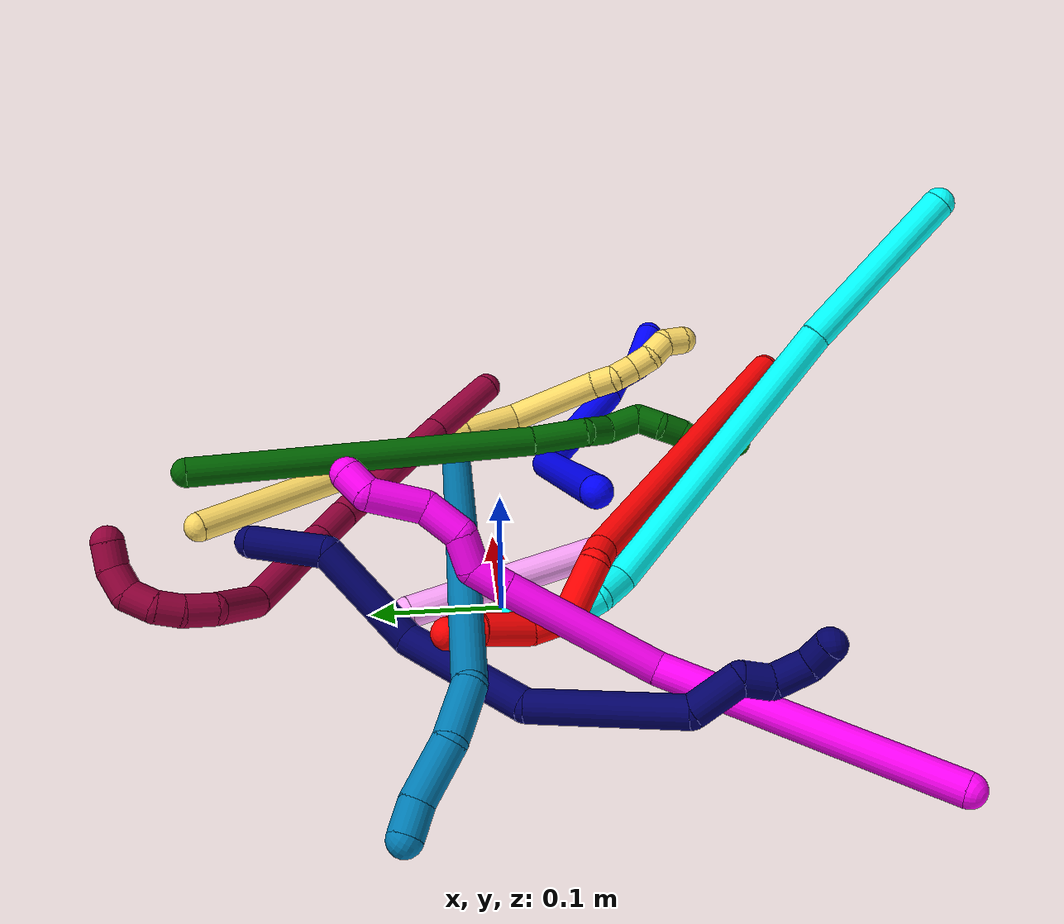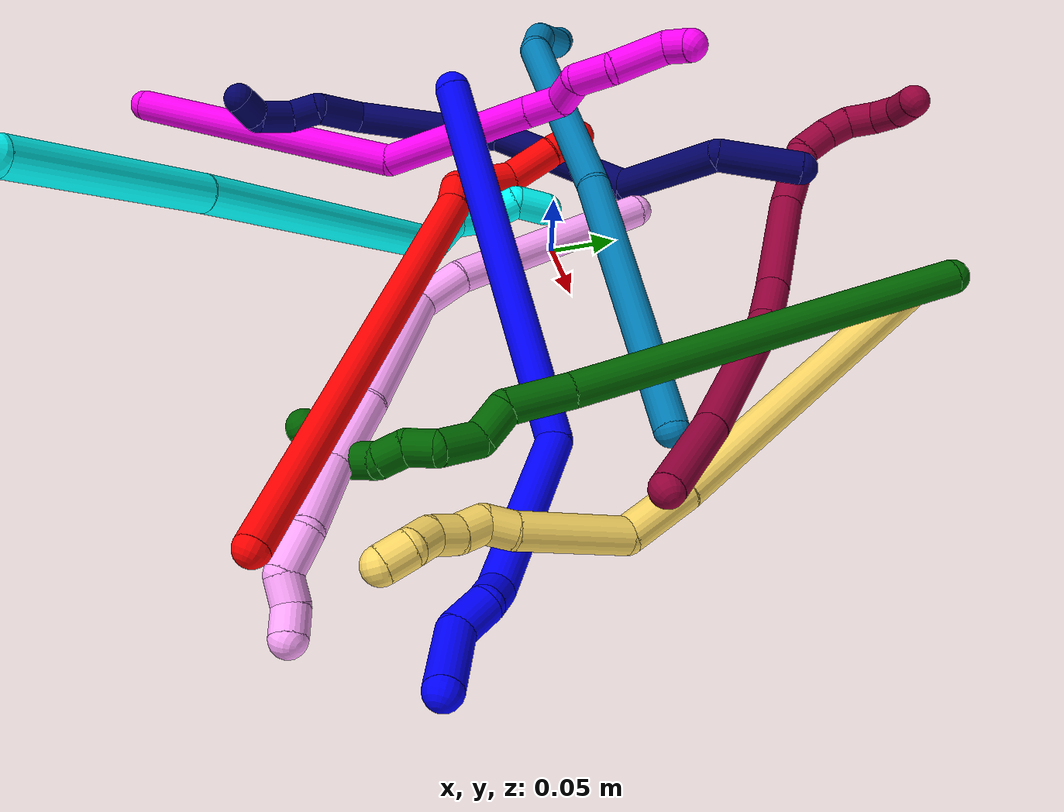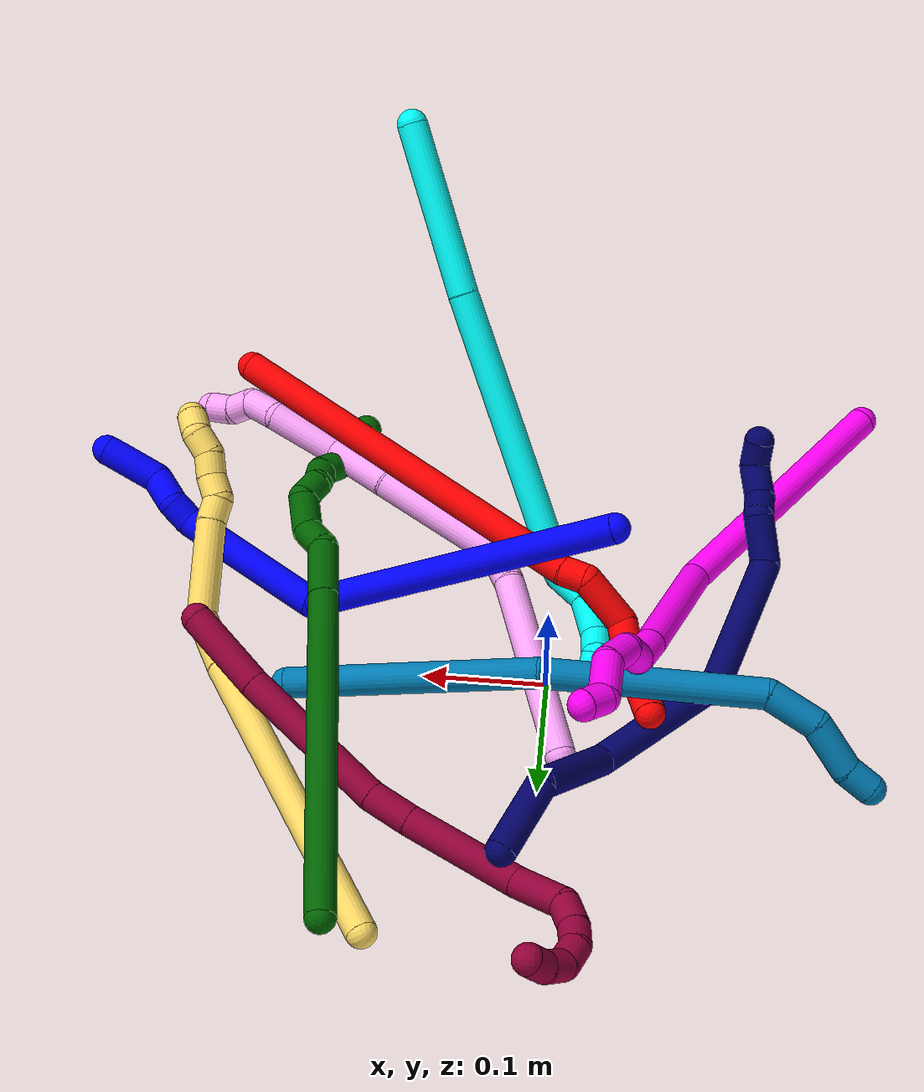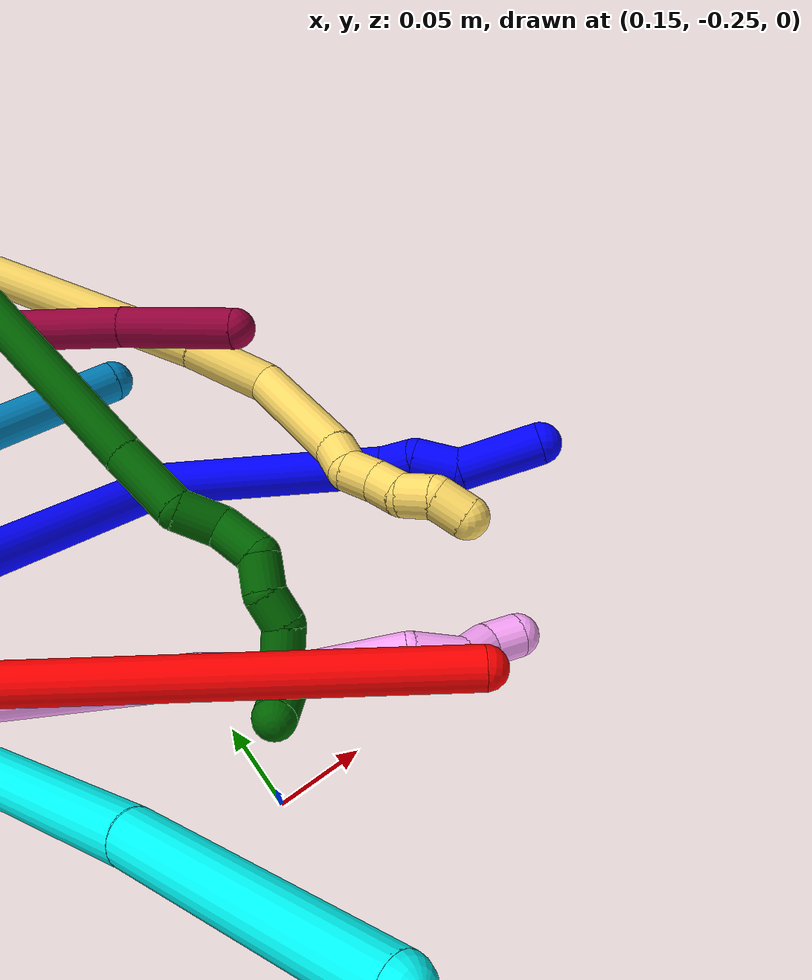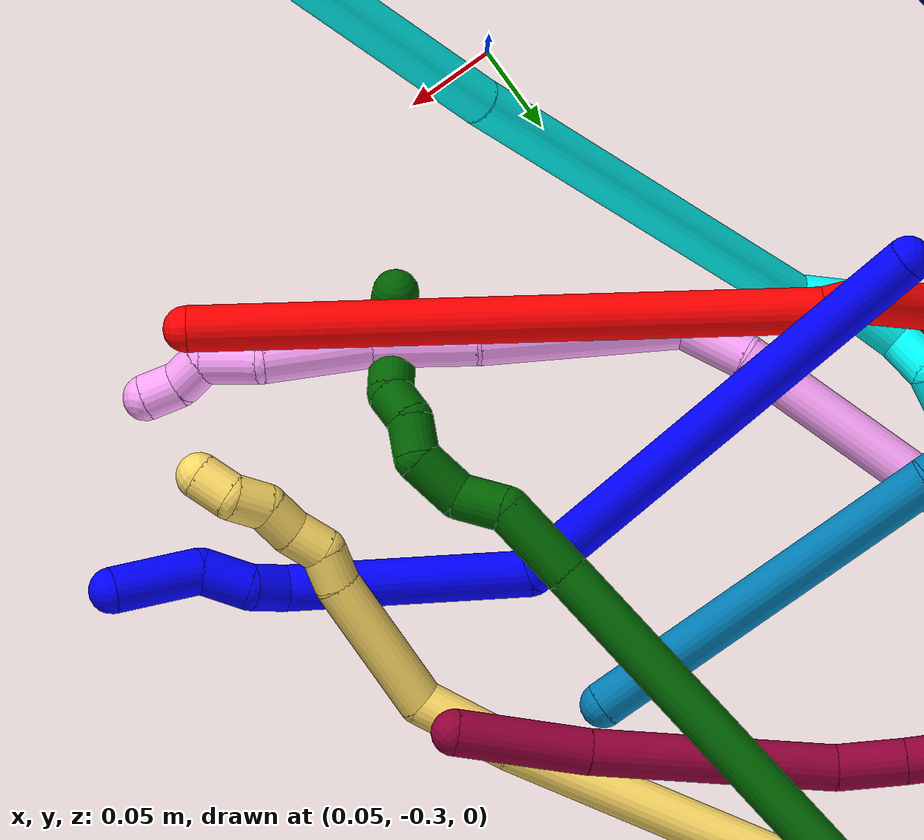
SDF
<sdf version="1.7">
 <world name="default">
  <plugin name="TubeGeneratorPlugin" filename="libtube_generator_plugin.so"/>
  <model name="photoneo_s_sensor">
   <static>1</static>
   <pose>0 0 2 1.57079 1.57079 3.14159</pose>
   <link name="link">
    <inertial><mass>0.1</mass></inertial>
    <sensor name="sensor" type="depth">
     <update_rate>30</update_rate>
     <camera>
      <horizontal_fov>1.22</horizontal_fov>
      <image><width>1920</width><height>1200</height><format>B8G8R8</format></image>
      <clip><near>0.1</near><far>4</far></clip>
      <depth_camera><output>points</output></depth_camera>
     </camera>
     <plugin name="camera_plugin" filename="libgazebo_ros_depth_camera.so">
      <baseline>0.2</baseline>
      <alwaysOn>1</alwaysOn>
      <updateRate>0.0</updateRate>
      <cameraName>camera_ir</cameraName>
      <imageTopicName>/camera/color/image_raw</imageTopicName>
      <cameraInfoTopicName>/camera/color/camera_info</cameraInfoTopicName>
      <depthImageTopicName>/camera/depth/image_raw</depthImageTopicName>
      <depthImageCameraInfoTopicName>/camera/depth/camera_info</depthImageCameraInfoTopicName>
      <pointCloudTopicName>/camera/depth/points</pointCloudTopicName>
      <frameName>fr_optical</frameName>
      <pointCloudCutoff>0.1</pointCloudCutoff>
      <pointCloudCutoffMax>2.0</pointCloudCutoffMax>
      <distortionK1>0</distortionK1>
      <distortionK2>0</distortionK2>
      <distortionK3>0</distortionK3>
      <distortionT1>0</distortionT1>
      <distortionT2>0</distortionT2>
      <CxPrime>0</CxPrime>
      <Cx>0</Cx>
      <Cy>0</Cy>
      <focalLength>0</focalLength>
      <hackBaseline>0</hackBaseline>
     </plugin>
    </sensor>
   </link>
  </model>
  <gravity>0 0 -9.8</gravity>
  <magnetic_field>6e-06 2.3e-05 -4.2e-05</magnetic_field>
  <atmosphere type="adiabatic"/>
  <physics name="default_physics" default="0" type="ode">
   <max_step_size>0.003</max_step_size>
   <real_time_factor>1</real_time_factor>
   <real_time_update_rate>1000</real_time_update_rate>
   <max_contacts>10000</max_contacts>
   <ode>
    <solver>
     <type>quick</type>
     <iters>100</iters>
     <sor>1.3</sor>
     <use_dynamic_moi_rescaling>0</use_dynamic_moi_rescaling>
    </solver>
    <constraints>
     <contact_max_correcting_vel>0</contact_max_correcting_vel>
     <contact_surface_layer>0.001</contact_surface_layer>
     <cfm>0</cfm>
     <erp>0.2</erp>
    </constraints>
   </ode>
  </physics>
  <scene><ambient>0.4 0.4 0.4 1</ambient><background>0.7 0.7 0.7 1</background><shadows>0</shadows></scene>
  <audio><device>default</device></audio>
  <spherical_coordinates>
   <surface_model>EARTH_WGS84</surface_model>
   <latitude_deg>0</latitude_deg>
   <longitude_deg>0</longitude_deg>
   <elevation>0</elevation>
   <heading_deg>0</heading_deg>
  </spherical_coordinates>
  <model name="bin">
   <static>1</static>
   <link name="bottom">
    <collision name="collision-bottom">
     <pose>0 0 -0.01 0 -0 0</pose>
     <geometry><box><size>0.8 0.6 0.02</size></box></geometry>
     <surface>
      <friction><ode><mu>100</mu><mu2>100</mu2></ode></friction>
      <contact><collide_bitmask>65535</collide_bitmask></contact>
     </surface>
    </collision>
   </link>
   <link name="west_wall">
    <collision name="collision-west_wall">
     <pose>-0.41 0 0.1 0 -0 0</pose>
     <geometry><box><size>0.02 0.6 0.2</size></box></geometry>
     <surface>
      <friction><ode><mu>100</mu><mu2>100</mu2></ode></friction>
      <contact><collide_bitmask>65535</collide_bitmask></contact>
     </surface>
    </collision>
   </link>
   <link name="east_wall">
    <collision name="collision-east_wall">
     <pose>0.41 0 0.1 0 -0 0</pose>
     <geometry><box><size>0.02 0.6 0.2</size></box></geometry>
     <surface>
      <friction><ode><mu>100</mu><mu2>100</mu2></ode></friction>
      <contact><collide_bitmask>65535</collide_bitmask></contact>
     </surface>
    </collision>
   </link>
   <link name="south_wall">
    <collision name="collision-south_wall">
     <pose>0 -0.31 0.1 0 -0 0</pose>
     <geometry><box><size>0.8 0.02 0.2</size></box></geometry>
     <surface>
      <friction><ode><mu>100</mu><mu2>100</mu2></ode></friction>
      <contact><collide_bitmask>65535</collide_bitmask></contact>
     </surface>
    </collision>
   </link>
   <link name="north_wall">
    <collision name="collision-north_wall">
     <pose>0 0.31 0.1 0 -0 0</pose>
     <geometry><box><size>0.8 0.02 0.2</size></box></geometry>
     <surface>
      <friction><ode><mu>100</mu><mu2>100</mu2></ode></friction>
      <contact><collide_bitmask>65535</collide_bitmask></contact>
     </surface>
    </collision>
   </link>
  </model>
  <model name="1">
   <static>0</static>
   <link name="1">
    <collision name="collision-cylinder-e_1_1_4">
     <pose>0.060408 -0.050287 0.110456 0.427228 0.461837 0.101915</pose>
     <geometry><cylinder><radius>0.0125</radius><length>0.271135</length></cylinder></geometry>
     <surface>
      <friction><ode><mu>1.16</mu><mu2>1.16</mu2><slip1>0</slip1><slip2>0</slip2></ode></friction>
      <contact><ode><kp>1e+06</kp><kd>1</kd><max_vel>0</max_vel><min_depth>0.001</min_depth></ode></contact>
     </surface>
    </collision>
    <visual name="visual-cylinder-e_1_1_4">
     <pose>0.060408 -0.050287 0.110456 0.427228 0.461837 0.101915</pose>
     <geometry><cylinder><radius>0.0125</radius><length>0.271135</length></cylinder></geometry>
     <material><ambient>0 0 1 1</ambient></material>
    </visual>
    <collision name="collision-cylinder-e_2_4_5">
     <pose>0.118556 -0.089332 0.285634 -0.171987 -0.034383 0.002964</pose>
     <geometry><cylinder><radius>0.0125</radius><length>0.13146</length></cylinder></geometry>
     <surface>
      <friction><ode><mu>1.16</mu><mu2>1.16</mu2><slip1>0</slip1><slip2>0</slip2></ode></friction>
      <contact><ode><kp>1e+06</kp><kd>1</kd><max_vel>0</max_vel><min_depth>0.001</min_depth></ode></contact>
     </surface>
    </collision>
    <visual name="visual-cylinder-e_2_4_5">
     <pose>0.118556 -0.089332 0.285634 -0.171987 -0.034383 0.002964</pose>
     <geometry><cylinder><radius>0.0125</radius><length>0.13146</length></cylinder></geometry>
     <material><ambient>0 0 1 1</ambient></material>
    </visual>
    <collision name="collision-cylinder-e_3_5_6">
     <pose>0.115973 -0.071719 0.358798 -0.646482 -0.030572 0.010242</pose>
     <geometry><cylinder><radius>0.0125</radius><length>0.021163</length></cylinder></geometry>
     <surface>
      <friction><ode><mu>1.16</mu><mu2>1.16</mu2><slip1>0</slip1><slip2>0</slip2></ode></friction>
      <contact><ode><kp>1e+06</kp><kd>1</kd><max_vel>0</max_vel><min_depth>0.001</min_depth></ode></contact>
     </surface>
    </collision>
    <visual name="visual-cylinder-e_3_5_6">
     <pose>0.115973 -0.071719 0.358798 -0.646482 -0.030572 0.010242</pose>
     <geometry><cylinder><radius>0.0125</radius><length>0.021163</length></cylinder></geometry>
     <material><ambient>0 0 1 1</ambient></material>
    </visual>
    <collision name="collision-cylinder-e_4_6_7">
     <pose>0.110298 -0.061851 0.379276 -0.282736 -0.403568 0.058211</pose>
     <geometry><cylinder><radius>0.0125</radius><length>0.027257</length></cylinder></geometry>
     <surface>
      <friction><ode><mu>1.16</mu><mu2>1.16</mu2><slip1>0</slip1><slip2>0</slip2></ode></friction>
      <contact><ode><kp>1e+06</kp><kd>1</kd><max_vel>0</max_vel><min_depth>0.001</min_depth></ode></contact>
     </surface>
    </collision>
    <visual name="visual-cylinder-e_4_6_7">
     <pose>0.110298 -0.061851 0.379276 -0.282736 -0.403568 0.058211</pose>
     <geometry><cylinder><radius>0.0125</radius><length>0.027257</length></cylinder></geometry>
     <material><ambient>0 0 1 1</ambient></material>
    </visual>
    <collision name="collision-cylinder-e_5_7_2">
     <pose>0.108742 -0.049977 0.414013 -0.353545 0.155615 -0.027853</pose>
     <geometry><cylinder><radius>0.0125</radius><length>0.048986</length></cylinder></geometry>
     <surface>
      <friction><ode><mu>1.16</mu><mu2>1.16</mu2><slip1>0</slip1><slip2>0</slip2></ode></friction>
      <contact><ode><kp>1e+06</kp><kd>1</kd><max_vel>0</max_vel><min_depth>0.001</min_depth></ode></contact>
     </surface>
    </collision>
    <visual name="visual-cylinder-e_5_7_2">
     <pose>0.108742 -0.049977 0.414013 -0.353545 0.155615 -0.027853</pose>
     <geometry><cylinder><radius>0.0125</radius><length>0.048986</length></cylinder></geometry>
     <material><ambient>0 0 1 1</ambient></material>
    </visual>
    <collision name="collision-sphere-2">
     <pose>0.112538 -0.041599 0.436713 0 -0 0</pose>
     <geometry><sphere><radius>0.0125</radius></sphere></geometry>
     <surface>
      <friction><ode><mu>1.16</mu><mu2>1.16</mu2><slip1>0</slip1><slip2>0</slip2></ode></friction>
      <contact><ode><kp>1e+06</kp><kd>1</kd><max_vel>0</max_vel><min_depth>0.001</min_depth></ode></contact>
     </surface>
    </collision>
    <visual name="visual-sphere-2">
     <pose>0.112538 -0.041599 0.436713 0 -0 0</pose>
     <geometry><sphere><radius>0.0125</radius></sphere></geometry>
     <material><ambient>0 0 1 1</ambient></material>
    </visual>
    <collision name="collision-sphere-7">
     <pose>0.104946 -0.058355 0.391313 0 -0 0</pose>
     <geometry><sphere><radius>0.0125</radius></sphere></geometry>
     <surface>
      <friction><ode><mu>1.16</mu><mu2>1.16</mu2><slip1>0</slip1><slip2>0</slip2></ode></friction>
      <contact><ode><kp>1e+06</kp><kd>1</kd><max_vel>0</max_vel><min_depth>0.001</min_depth></ode></contact>
     </surface>
    </collision>
    <visual name="visual-sphere-7">
     <pose>0.104946 -0.058355 0.391313 0 -0 0</pose>
     <geometry><sphere><radius>0.0125</radius></sphere></geometry>
     <material><ambient>0 0 1 1</ambient></material>
    </visual>
    <collision name="collision-sphere-6">
     <pose>0.11565 -0.065348 0.36724 0 -0 0</pose>
     <geometry><sphere><radius>0.0125</radius></sphere></geometry>
     <surface>
      <friction><ode><mu>1.16</mu><mu2>1.16</mu2><slip1>0</slip1><slip2>0</slip2></ode></friction>
      <contact><ode><kp>1e+06</kp><kd>1</kd><max_vel>0</max_vel><min_depth>0.001</min_depth></ode></contact>
     </surface>
    </collision>
    <visual name="visual-sphere-6">
     <pose>0.11565 -0.065348 0.36724 0 -0 0</pose>
     <geometry><sphere><radius>0.0125</radius></sphere></geometry>
     <material><ambient>0 0 1 1</ambient></material>
    </visual>
    <collision name="collision-sphere-5">
     <pose>0.116297 -0.07809 0.350356 0 -0 0</pose>
     <geometry><sphere><radius>0.0125</radius></sphere></geometry>
     <surface>
      <friction><ode><mu>1.16</mu><mu2>1.16</mu2><slip1>0</slip1><slip2>0</slip2></ode></friction>
      <contact><ode><kp>1e+06</kp><kd>1</kd><max_vel>0</max_vel><min_depth>0.001</min_depth></ode></contact>
     </surface>
    </collision>
    <visual name="visual-sphere-5">
     <pose>0.116297 -0.07809 0.350356 0 -0 0</pose>
     <geometry><sphere><radius>0.0125</radius></sphere></geometry>
     <material><ambient>0 0 1 1</ambient></material>
    </visual>
    <collision name="collision-sphere-1">
     <geometry><sphere><radius>0.0125</radius></sphere></geometry>
     <surface>
      <friction><ode><mu>1.16</mu><mu2>1.16</mu2><slip1>0</slip1><slip2>0</slip2></ode></friction>
      <contact><ode><kp>1e+06</kp><kd>1</kd><max_vel>0</max_vel><min_depth>0.001</min_depth></ode></contact>
     </surface>
    </collision>
    <visual name="visual-sphere-1">
     <geometry><sphere><radius>0.0125</radius></sphere></geometry>
     <material><ambient>0 0 1 1</ambient></material>
    </visual>
    <collision name="collision-sphere-4">
     <pose>0.120816 -0.100575 0.220912 0 -0 0</pose>
     <geometry><sphere><radius>0.0125</radius></sphere></geometry>
     <surface>
      <friction><ode><mu>1.16</mu><mu2>1.16</mu2><slip1>0</slip1><slip2>0</slip2></ode></friction>
      <contact><ode><kp>1e+06</kp><kd>1</kd><max_vel>0</max_vel><min_depth>0.001</min_depth></ode></contact>
     </surface>
    </collision>
    <visual name="visual-sphere-4">
     <pose>0.120816 -0.100575 0.220912 0 -0 0</pose>
     <geometry><sphere><radius>0.0125</radius></sphere></geometry>
     <material><ambient>0 0 1 1</ambient></material>
    </visual>
    <inertial>
     <pose>0.085503 -0.06206 0.21142 0 -0 0</pose>
     <mass>0.5</mass>
     <inertia>
      <ixx>0.00186</ixx>
      <ixy>0</ixy>
      <ixz>0</ixz>
      <iyy>0.001901</iyy>
      <iyz>0</iyz>
      <izz>-0.000124</izz>
     </inertia>
    </inertial>
   </link>
   <pose>-0.0463 -0.065961 0.129775 1.69762 -0.075373 1.05175</pose>
  </model>
  <model name="2">
   <static>0</static>
   <link name="2">
    <collision name="collision-cylinder-e_1_1_4">
     <pose>-0.030413 0.060938 -0.154097 -2.76501 -0.181513 0.891142</pose>
     <geometry><cylinder><radius>0.0125</radius><length>0.336953</length></cylinder></geometry>
     <surface>
      <friction><ode><mu>1.16</mu><mu2>1.16</mu2><slip1>0</slip1><slip2>0</slip2></ode></friction>
      <contact><ode><kp>1e+06</kp><kd>1</kd><max_vel>0</max_vel><min_depth>0.001</min_depth></ode></contact>
     </surface>
    </collision>
    <visual name="visual-cylinder-e_1_1_4">
     <pose>-0.030413 0.060938 -0.154097 -2.76501 -0.181513 0.891142</pose>
     <geometry><cylinder><radius>0.0125</radius><length>0.336953</length></cylinder></geometry>
     <material><ambient>1 0 0 1</ambient></material>
    </visual>
    <collision name="collision-cylinder-e_2_4_5">
     <pose>-0.060525 0.126444 -0.317573 -2.6884 0.028831 -0.124898</pose>
     <geometry><cylinder><radius>0.0125</radius><length>0.020872</length></cylinder></geometry>
     <surface>
      <friction><ode><mu>1.16</mu><mu2>1.16</mu2><slip1>0</slip1><slip2>0</slip2></ode></friction>
      <contact><ode><kp>1e+06</kp><kd>1</kd><max_vel>0</max_vel><min_depth>0.001</min_depth></ode></contact>
     </surface>
    </collision>
    <visual name="visual-cylinder-e_2_4_5">
     <pose>-0.060525 0.126444 -0.317573 -2.6884 0.028831 -0.124898</pose>
     <geometry><cylinder><radius>0.0125</radius><length>0.020872</length></cylinder></geometry>
     <material><ambient>1 0 0 1</ambient></material>
    </visual>
    <collision name="collision-cylinder-e_3_5_6">
     <pose>-0.071664 0.145927 -0.339797 -2.28174 -0.526466 1.06268</pose>
     <geometry><cylinder><radius>0.0125</radius><length>0.045534</length></cylinder></geometry>
     <surface>
      <friction><ode><mu>1.16</mu><mu2>1.16</mu2><slip1>0</slip1><slip2>0</slip2></ode></friction>
      <contact><ode><kp>1e+06</kp><kd>1</kd><max_vel>0</max_vel><min_depth>0.001</min_depth></ode></contact>
     </surface>
    </collision>
    <visual name="visual-cylinder-e_3_5_6">
     <pose>-0.071664 0.145927 -0.339797 -2.28174 -0.526466 1.06268</pose>
     <geometry><cylinder><radius>0.0125</radius><length>0.045534</length></cylinder></geometry>
     <material><ambient>1 0 0 1</ambient></material>
    </visual>
    <collision name="collision-cylinder-e_4_6_7">
     <pose>-0.094453 0.160007 -0.362567 3.05764 -0.850475 -2.95664</pose>
     <geometry><cylinder><radius>0.0125</radius><length>0.0302</length></cylinder></geometry>
     <surface>
      <friction><ode><mu>1.16</mu><mu2>1.16</mu2><slip1>0</slip1><slip2>0</slip2></ode></friction>
      <contact><ode><kp>1e+06</kp><kd>1</kd><max_vel>0</max_vel><min_depth>0.001</min_depth></ode></contact>
     </surface>
    </collision>
    <visual name="visual-cylinder-e_4_6_7">
     <pose>-0.094453 0.160007 -0.362567 3.05764 -0.850475 -2.95664</pose>
     <geometry><cylinder><radius>0.0125</radius><length>0.0302</length></cylinder></geometry>
     <material><ambient>1 0 0 1</ambient></material>
    </visual>
    <collision name="collision-cylinder-e_5_7_8">
     <pose>-0.114268 0.153287 -0.389396 2.80659 -0.441794 -1.85082</pose>
     <geometry><cylinder><radius>0.0125</radius><length>0.0396</length></cylinder></geometry>
     <surface>
      <friction><ode><mu>1.16</mu><mu2>1.16</mu2><slip1>0</slip1><slip2>0</slip2></ode></friction>
      <contact><ode><kp>1e+06</kp><kd>1</kd><max_vel>0</max_vel><min_depth>0.001</min_depth></ode></contact>
     </surface>
    </collision>
    <visual name="visual-cylinder-e_5_7_8">
     <pose>-0.114268 0.153287 -0.389396 2.80659 -0.441794 -1.85082</pose>
     <geometry><cylinder><radius>0.0125</radius><length>0.0396</length></cylinder></geometry>
     <material><ambient>1 0 0 1</ambient></material>
    </visual>
    <collision name="collision-cylinder-e_6_8_2">
     <pose>-0.129403 0.144486 -0.417575 2.88848 -0.520087 -2.24945</pose>
     <geometry><cylinder><radius>0.0125</radius><length>0.02684</length></cylinder></geometry>
     <surface>
      <friction><ode><mu>1.16</mu><mu2>1.16</mu2><slip1>0</slip1><slip2>0</slip2></ode></friction>
      <contact><ode><kp>1e+06</kp><kd>1</kd><max_vel>0</max_vel><min_depth>0.001</min_depth></ode></contact>
     </surface>
    </collision>
    <visual name="visual-cylinder-e_6_8_2">
     <pose>-0.129403 0.144486 -0.417575 2.88848 -0.520087 -2.24945</pose>
     <geometry><cylinder><radius>0.0125</radius><length>0.02684</length></cylinder></geometry>
     <material><ambient>1 0 0 1</ambient></material>
    </visual>
    <collision name="collision-sphere-2">
     <pose>-0.136072 0.14157 -0.42885 0 -0 0</pose>
     <geometry><sphere><radius>0.0125</radius></sphere></geometry>
     <surface>
      <friction><ode><mu>1.16</mu><mu2>1.16</mu2><slip1>0</slip1><slip2>0</slip2></ode></friction>
      <contact><ode><kp>1e+06</kp><kd>1</kd><max_vel>0</max_vel><min_depth>0.001</min_depth></ode></contact>
     </surface>
    </collision>
    <visual name="visual-sphere-2">
     <pose>-0.136072 0.14157 -0.42885 0 -0 0</pose>
     <geometry><sphere><radius>0.0125</radius></sphere></geometry>
     <material><ambient>1 0 0 1</ambient></material>
    </visual>
    <collision name="collision-sphere-4">
     <pose>-0.060826 0.121877 -0.308195 0 -0 0</pose>
     <geometry><sphere><radius>0.0125</radius></sphere></geometry>
     <surface>
      <friction><ode><mu>1.16</mu><mu2>1.16</mu2><slip1>0</slip1><slip2>0</slip2></ode></friction>
      <contact><ode><kp>1e+06</kp><kd>1</kd><max_vel>0</max_vel><min_depth>0.001</min_depth></ode></contact>
     </surface>
    </collision>
    <visual name="visual-sphere-4">
     <pose>-0.060826 0.121877 -0.308195 0 -0 0</pose>
     <geometry><sphere><radius>0.0125</radius></sphere></geometry>
     <material><ambient>1 0 0 1</ambient></material>
    </visual>
    <collision name="collision-sphere-1">
     <geometry><sphere><radius>0.0125</radius></sphere></geometry>
     <surface>
      <friction><ode><mu>1.16</mu><mu2>1.16</mu2><slip1>0</slip1><slip2>0</slip2></ode></friction>
      <contact><ode><kp>1e+06</kp><kd>1</kd><max_vel>0</max_vel><min_depth>0.001</min_depth></ode></contact>
     </surface>
    </collision>
    <visual name="visual-sphere-1">
     <geometry><sphere><radius>0.0125</radius></sphere></geometry>
     <material><ambient>1 0 0 1</ambient></material>
    </visual>
    <collision name="collision-sphere-8">
     <pose>-0.122734 0.147402 -0.4063 0 -0 0</pose>
     <geometry><sphere><radius>0.0125</radius></sphere></geometry>
     <surface>
      <friction><ode><mu>1.16</mu><mu2>1.16</mu2><slip1>0</slip1><slip2>0</slip2></ode></friction>
      <contact><ode><kp>1e+06</kp><kd>1</kd><max_vel>0</max_vel><min_depth>0.001</min_depth></ode></contact>
     </surface>
    </collision>
    <visual name="visual-sphere-8">
     <pose>-0.122734 0.147402 -0.4063 0 -0 0</pose>
     <geometry><sphere><radius>0.0125</radius></sphere></geometry>
     <material><ambient>1 0 0 1</ambient></material>
    </visual>
    <collision name="collision-sphere-5">
     <pose>-0.060224 0.131011 -0.326952 0 -0 0</pose>
     <geometry><sphere><radius>0.0125</radius></sphere></geometry>
     <surface>
      <friction><ode><mu>1.16</mu><mu2>1.16</mu2><slip1>0</slip1><slip2>0</slip2></ode></friction>
      <contact><ode><kp>1e+06</kp><kd>1</kd><max_vel>0</max_vel><min_depth>0.001</min_depth></ode></contact>
     </surface>
    </collision>
    <visual name="visual-sphere-5">
     <pose>-0.060224 0.131011 -0.326952 0 -0 0</pose>
     <geometry><sphere><radius>0.0125</radius></sphere></geometry>
     <material><ambient>1 0 0 1</ambient></material>
    </visual>
    <collision name="collision-sphere-6">
     <pose>-0.083104 0.160842 -0.352642 0 -0 0</pose>
     <geometry><sphere><radius>0.0125</radius></sphere></geometry>
     <surface>
      <friction><ode><mu>1.16</mu><mu2>1.16</mu2><slip1>0</slip1><slip2>0</slip2></ode></friction>
      <contact><ode><kp>1e+06</kp><kd>1</kd><max_vel>0</max_vel><min_depth>0.001</min_depth></ode></contact>
     </surface>
    </collision>
    <visual name="visual-sphere-6">
     <pose>-0.083104 0.160842 -0.352642 0 -0 0</pose>
     <geometry><sphere><radius>0.0125</radius></sphere></geometry>
     <material><ambient>1 0 0 1</ambient></material>
    </visual>
    <collision name="collision-sphere-7">
     <pose>-0.105802 0.159172 -0.372492 0 -0 0</pose>
     <geometry><sphere><radius>0.0125</radius></sphere></geometry>
     <surface>
      <friction><ode><mu>1.16</mu><mu2>1.16</mu2><slip1>0</slip1><slip2>0</slip2></ode></friction>
      <contact><ode><kp>1e+06</kp><kd>1</kd><max_vel>0</max_vel><min_depth>0.001</min_depth></ode></contact>
     </surface>
    </collision>
    <visual name="visual-sphere-7">
     <pose>-0.105802 0.159172 -0.372492 0 -0 0</pose>
     <geometry><sphere><radius>0.0125</radius></sphere></geometry>
     <material><ambient>1 0 0 1</ambient></material>
    </visual>
    <inertial>
     <pose>-0.05125 0.089195 -0.223204 0 -0 0</pose>
     <mass>0.5</mass>
     <inertia>
      <ixx>0.004417</ixx>
      <ixy>0</ixy>
      <ixz>0</ixz>
      <iyy>0.00076</iyy>
      <iyz>0</iyz>
      <izz>-0.000606</izz>
     </inertia>
    </inertial>
   </link>
   <pose>0.273063 -0.263285 0.057306 -2.07994 -0.667553 -1.93671</pose>
  </model>
  <model name="3">
   <static>0</static>
   <link name="3">
    <collision name="collision-cylinder-e_1_1_4">
     <pose>0.003489 0.028639 -0.065552 -2.7297 0.048728 -0.232246</pose>
     <geometry><cylinder><radius>0.0125</radius><length>0.14324</length></cylinder></geometry>
     <surface>
      <friction><ode><mu>1.16</mu><mu2>1.16</mu2><slip1>0</slip1><slip2>0</slip2></ode></friction>
      <contact><ode><kp>1e+06</kp><kd>1</kd><max_vel>0</max_vel><min_depth>0.001</min_depth></ode></contact>
     </surface>
    </collision>
    <visual name="visual-cylinder-e_1_1_4">
     <pose>0.003489 0.028639 -0.065552 -2.7297 0.048728 -0.232246</pose>
     <geometry><cylinder><radius>0.0125</radius><length>0.14324</length></cylinder></geometry>
     <material><ambient>0.003922 1 0.996078 1</ambient></material>
    </visual>
    <collision name="collision-cylinder-e_2_4_5">
     <pose>0.008766 0.098753 -0.24479 -2.79177 0.01478 -0.083589</pose>
     <geometry><cylinder><radius>0.0125</radius><length>0.242057</length></cylinder></geometry>
     <surface>
      <friction><ode><mu>1.16</mu><mu2>1.16</mu2><slip1>0</slip1><slip2>0</slip2></ode></friction>
      <contact><ode><kp>1e+06</kp><kd>1</kd><max_vel>0</max_vel><min_depth>0.001</min_depth></ode></contact>
     </surface>
    </collision>
    <visual name="visual-cylinder-e_2_4_5">
     <pose>0.008766 0.098753 -0.24479 -2.79177 0.01478 -0.083589</pose>
     <geometry><cylinder><radius>0.0125</radius><length>0.242057</length></cylinder></geometry>
     <material><ambient>0.003922 1 0.996078 1</ambient></material>
    </visual>
    <collision name="collision-cylinder-e_3_5_6">
     <pose>0.003213 0.15024 -0.367051 -2.27899 -0.508147 1.0275</pose>
     <geometry><cylinder><radius>0.0125</radius><length>0.030177</length></cylinder></geometry>
     <surface>
      <friction><ode><mu>1.16</mu><mu2>1.16</mu2><slip1>0</slip1><slip2>0</slip2></ode></friction>
      <contact><ode><kp>1e+06</kp><kd>1</kd><max_vel>0</max_vel><min_depth>0.001</min_depth></ode></contact>
     </surface>
    </collision>
    <visual name="visual-cylinder-e_3_5_6">
     <pose>0.003213 0.15024 -0.367051 -2.27899 -0.508147 1.0275</pose>
     <geometry><cylinder><radius>0.0125</radius><length>0.030177</length></cylinder></geometry>
     <material><ambient>0.003922 1 0.996078 1</ambient></material>
    </visual>
    <collision name="collision-cylinder-e_4_6_7">
     <pose>-0.003724 0.17144 -0.387781 -2.39765 0.024491 -0.062759</pose>
     <geometry><cylinder><radius>0.0125</radius><length>0.033052</length></cylinder></geometry>
     <surface>
      <friction><ode><mu>1.16</mu><mu2>1.16</mu2><slip1>0</slip1><slip2>0</slip2></ode></friction>
      <contact><ode><kp>1e+06</kp><kd>1</kd><max_vel>0</max_vel><min_depth>0.001</min_depth></ode></contact>
     </surface>
    </collision>
    <visual name="visual-cylinder-e_4_6_7">
     <pose>-0.003724 0.17144 -0.387781 -2.39765 0.024491 -0.062759</pose>
     <geometry><cylinder><radius>0.0125</radius><length>0.033052</length></cylinder></geometry>
     <material><ambient>0.003922 1 0.996078 1</ambient></material>
    </visual>
    <collision name="collision-cylinder-e_5_7_8">
     <pose>-0.001992 0.195581 -0.40145 -1.68698 0.101392 -0.113889</pose>
     <geometry><cylinder><radius>0.0125</radius><length>0.026217</length></cylinder></geometry>
     <surface>
      <friction><ode><mu>1.16</mu><mu2>1.16</mu2><slip1>0</slip1><slip2>0</slip2></ode></friction>
      <contact><ode><kp>1e+06</kp><kd>1</kd><max_vel>0</max_vel><min_depth>0.001</min_depth></ode></contact>
     </surface>
    </collision>
    <visual name="visual-cylinder-e_5_7_8">
     <pose>-0.001992 0.195581 -0.40145 -1.68698 0.101392 -0.113889</pose>
     <geometry><cylinder><radius>0.0125</radius><length>0.026217</length></cylinder></geometry>
     <material><ambient>0.003922 1 0.996078 1</ambient></material>
    </visual>
    <collision name="collision-cylinder-e_6_8_2">
     <pose>0.005206 0.216325 -0.410981 -2.37075 0.483549 -1.09229</pose>
     <geometry><cylinder><radius>0.0125</radius><length>0.025257</length></cylinder></geometry>
     <surface>
      <friction><ode><mu>1.16</mu><mu2>1.16</mu2><slip1>0</slip1><slip2>0</slip2></ode></friction>
      <contact><ode><kp>1e+06</kp><kd>1</kd><max_vel>0</max_vel><min_depth>0.001</min_depth></ode></contact>
     </surface>
    </collision>
    <visual name="visual-cylinder-e_6_8_2">
     <pose>0.005206 0.216325 -0.410981 -2.37075 0.483549 -1.09229</pose>
     <geometry><cylinder><radius>0.0125</radius><length>0.025257</length></cylinder></geometry>
     <material><ambient>0.003922 1 0.996078 1</ambient></material>
    </visual>
    <collision name="collision-sphere-2">
     <pose>0.011077 0.224115 -0.419002 0 -0 0</pose>
     <geometry><sphere><radius>0.0125</radius></sphere></geometry>
     <surface>
      <friction><ode><mu>1.16</mu><mu2>1.16</mu2><slip1>0</slip1><slip2>0</slip2></ode></friction>
      <contact><ode><kp>1e+06</kp><kd>1</kd><max_vel>0</max_vel><min_depth>0.001</min_depth></ode></contact>
     </surface>
    </collision>
    <visual name="visual-sphere-2">
     <pose>0.011077 0.224115 -0.419002 0 -0 0</pose>
     <geometry><sphere><radius>0.0125</radius></sphere></geometry>
     <material><ambient>0.003922 1 0.996078 1</ambient></material>
    </visual>
    <collision name="collision-sphere-4">
     <pose>0.006977 0.057277 -0.131104 0 -0 0</pose>
     <geometry><sphere><radius>0.0125</radius></sphere></geometry>
     <surface>
      <friction><ode><mu>1.16</mu><mu2>1.16</mu2><slip1>0</slip1><slip2>0</slip2></ode></friction>
      <contact><ode><kp>1e+06</kp><kd>1</kd><max_vel>0</max_vel><min_depth>0.001</min_depth></ode></contact>
     </surface>
    </collision>
    <visual name="visual-sphere-4">
     <pose>0.006977 0.057277 -0.131104 0 -0 0</pose>
     <geometry><sphere><radius>0.0125</radius></sphere></geometry>
     <material><ambient>0.003922 1 0.996078 1</ambient></material>
    </visual>
    <collision name="collision-sphere-1">
     <geometry><sphere><radius>0.0125</radius></sphere></geometry>
     <surface>
      <friction><ode><mu>1.16</mu><mu2>1.16</mu2><slip1>0</slip1><slip2>0</slip2></ode></friction>
      <contact><ode><kp>1e+06</kp><kd>1</kd><max_vel>0</max_vel><min_depth>0.001</min_depth></ode></contact>
     </surface>
    </collision>
    <visual name="visual-sphere-1">
     <geometry><sphere><radius>0.0125</radius></sphere></geometry>
     <material><ambient>0.003922 1 0.996078 1</ambient></material>
    </visual>
    <collision name="collision-sphere-8">
     <pose>-0.000665 0.208535 -0.402961 0 -0 0</pose>
     <geometry><sphere><radius>0.0125</radius></sphere></geometry>
     <surface>
      <friction><ode><mu>1.16</mu><mu2>1.16</mu2><slip1>0</slip1><slip2>0</slip2></ode></friction>
      <contact><ode><kp>1e+06</kp><kd>1</kd><max_vel>0</max_vel><min_depth>0.001</min_depth></ode></contact>
     </surface>
    </collision>
    <visual name="visual-sphere-8">
     <pose>-0.000665 0.208535 -0.402961 0 -0 0</pose>
     <geometry><sphere><radius>0.0125</radius></sphere></geometry>
     <material><ambient>0.003922 1 0.996078 1</ambient></material>
    </visual>
    <collision name="collision-sphere-5">
     <pose>0.010554 0.140228 -0.358476 0 -0 0</pose>
     <geometry><sphere><radius>0.0125</radius></sphere></geometry>
     <surface>
      <friction><ode><mu>1.16</mu><mu2>1.16</mu2><slip1>0</slip1><slip2>0</slip2></ode></friction>
      <contact><ode><kp>1e+06</kp><kd>1</kd><max_vel>0</max_vel><min_depth>0.001</min_depth></ode></contact>
     </surface>
    </collision>
    <visual name="visual-sphere-5">
     <pose>0.010554 0.140228 -0.358476 0 -0 0</pose>
     <geometry><sphere><radius>0.0125</radius></sphere></geometry>
     <material><ambient>0.003922 1 0.996078 1</ambient></material>
    </visual>
    <collision name="collision-sphere-6">
     <pose>-0.004128 0.160252 -0.375625 0 -0 0</pose>
     <geometry><sphere><radius>0.0125</radius></sphere></geometry>
     <surface>
      <friction><ode><mu>1.16</mu><mu2>1.16</mu2><slip1>0</slip1><slip2>0</slip2></ode></friction>
      <contact><ode><kp>1e+06</kp><kd>1</kd><max_vel>0</max_vel><min_depth>0.001</min_depth></ode></contact>
     </surface>
    </collision>
    <visual name="visual-sphere-6">
     <pose>-0.004128 0.160252 -0.375625 0 -0 0</pose>
     <geometry><sphere><radius>0.0125</radius></sphere></geometry>
     <material><ambient>0.003922 1 0.996078 1</ambient></material>
    </visual>
    <collision name="collision-sphere-7">
     <pose>-0.003319 0.182628 -0.399938 0 -0 0</pose>
     <geometry><sphere><radius>0.0125</radius></sphere></geometry>
     <surface>
      <friction><ode><mu>1.16</mu><mu2>1.16</mu2><slip1>0</slip1><slip2>0</slip2></ode></friction>
      <contact><ode><kp>1e+06</kp><kd>1</kd><max_vel>0</max_vel><min_depth>0.001</min_depth></ode></contact>
     </surface>
    </collision>
    <visual name="visual-sphere-7">
     <pose>-0.003319 0.182628 -0.399938 0 -0 0</pose>
     <geometry><sphere><radius>0.0125</radius></sphere></geometry>
     <material><ambient>0.003922 1 0.996078 1</ambient></material>
    </visual>
    <inertial>
     <pose>0.005349 0.097595 -0.226883 0 -0 0</pose>
     <mass>0.5</mass>
     <inertia>
      <ixx>0.001284</ixx>
      <ixy>0</ixy>
      <ixz>0</ixz>
      <iyy>-0.00148</iyy>
      <iyz>0</iyz>
      <izz>-0.00058</izz>
     </inertia>
    </inertial>
   </link>
   <pose>0.141015 -0.357655 0.263747 0.501543 0.292744 0.293979</pose>
  </model>
  <model name="4">
   <static>0</static>
   <link name="4">
    <collision name="collision-cylinder-e_1_1_4">
     <pose>0.076111 0.023106 -0.017977 -2.23198 1.2036 -1.90411</pose>
     <geometry><cylinder><radius>0.0125</radius><length>0.163094</length></cylinder></geometry>
     <surface>
      <friction><ode><mu>1.16</mu><mu2>1.16</mu2><slip1>0</slip1><slip2>0</slip2></ode></friction>
      <contact><ode><kp>1e+06</kp><kd>1</kd><max_vel>0</max_vel><min_depth>0.001</min_depth></ode></contact>
     </surface>
    </collision>
    <visual name="visual-cylinder-e_1_1_4">
     <pose>0.076111 0.023106 -0.017977 -2.23198 1.2036 -1.90411</pose>
     <geometry><cylinder><radius>0.0125</radius><length>0.163094</length></cylinder></geometry>
     <material><ambient>1 0.65098 0.996078 1</ambient></material>
    </visual>
    <collision name="collision-cylinder-e_2_4_5">
     <pose>0.168482 0.055141 -0.038674 -1.86653 1.0497 -1.32697</pose>
     <geometry><cylinder><radius>0.0125</radius><length>0.037498</length></cylinder></geometry>
     <surface>
      <friction><ode><mu>1.16</mu><mu2>1.16</mu2><slip1>0</slip1><slip2>0</slip2></ode></friction>
      <contact><ode><kp>1e+06</kp><kd>1</kd><max_vel>0</max_vel><min_depth>0.001</min_depth></ode></contact>
     </surface>
    </collision>
    <visual name="visual-cylinder-e_2_4_5">
     <pose>0.168482 0.055141 -0.038674 -1.86653 1.0497 -1.32697</pose>
     <geometry><cylinder><radius>0.0125</radius><length>0.037498</length></cylinder></geometry>
     <material><ambient>1 0.65098 0.996078 1</ambient></material>
    </visual>
    <collision name="collision-cylinder-e_3_5_6">
     <pose>0.228763 0.086405 -0.01652 -0.731683 0.921288 -0.375731</pose>
     <geometry><cylinder><radius>0.0125</radius><length>0.110552</length></cylinder></geometry>
     <surface>
      <friction><ode><mu>1.16</mu><mu2>1.16</mu2><slip1>0</slip1><slip2>0</slip2></ode></friction>
      <contact><ode><kp>1e+06</kp><kd>1</kd><max_vel>0</max_vel><min_depth>0.001</min_depth></ode></contact>
     </surface>
    </collision>
    <visual name="visual-cylinder-e_3_5_6">
     <pose>0.228763 0.086405 -0.01652 -0.731683 0.921288 -0.375731</pose>
     <geometry><cylinder><radius>0.0125</radius><length>0.110552</length></cylinder></geometry>
     <material><ambient>1 0.65098 0.996078 1</ambient></material>
    </visual>
    <collision name="collision-cylinder-e_4_6_7">
     <pose>0.295157 0.12368 0.018154 -0.99023 0.896921 -0.508387</pose>
     <geometry><cylinder><radius>0.0125</radius><length>0.057262</length></cylinder></geometry>
     <surface>
      <friction><ode><mu>1.16</mu><mu2>1.16</mu2><slip1>0</slip1><slip2>0</slip2></ode></friction>
      <contact><ode><kp>1e+06</kp><kd>1</kd><max_vel>0</max_vel><min_depth>0.001</min_depth></ode></contact>
     </surface>
    </collision>
    <visual name="visual-cylinder-e_4_6_7">
     <pose>0.295157 0.12368 0.018154 -0.99023 0.896921 -0.508387</pose>
     <geometry><cylinder><radius>0.0125</radius><length>0.057262</length></cylinder></geometry>
     <material><ambient>1 0.65098 0.996078 1</ambient></material>
    </visual>
    <collision name="collision-cylinder-e_5_7_8">
     <pose>0.340907 0.149239 0.043586 -0.596738 0.890948 -0.291616</pose>
     <geometry><cylinder><radius>0.0125</radius><length>0.060124</length></cylinder></geometry>
     <surface>
      <friction><ode><mu>1.16</mu><mu2>1.16</mu2><slip1>0</slip1><slip2>0</slip2></ode></friction>
      <contact><ode><kp>1e+06</kp><kd>1</kd><max_vel>0</max_vel><min_depth>0.001</min_depth></ode></contact>
     </surface>
    </collision>
    <visual name="visual-cylinder-e_5_7_8">
     <pose>0.340907 0.149239 0.043586 -0.596738 0.890948 -0.291616</pose>
     <geometry><cylinder><radius>0.0125</radius><length>0.060124</length></cylinder></geometry>
     <material><ambient>1 0.65098 0.996078 1</ambient></material>
    </visual>
    <collision name="collision-cylinder-e_6_8_9">
     <pose>0.375247 0.170398 0.062882 -1.23631 0.776582 -0.566159</pose>
     <geometry><cylinder><radius>0.0125</radius><length>0.031281</length></cylinder></geometry>
     <surface>
      <friction><ode><mu>1.16</mu><mu2>1.16</mu2><slip1>0</slip1><slip2>0</slip2></ode></friction>
      <contact><ode><kp>1e+06</kp><kd>1</kd><max_vel>0</max_vel><min_depth>0.001</min_depth></ode></contact>
     </surface>
    </collision>
    <visual name="visual-cylinder-e_6_8_9">
     <pose>0.375247 0.170398 0.062882 -1.23631 0.776582 -0.566159</pose>
     <geometry><cylinder><radius>0.0125</radius><length>0.031281</length></cylinder></geometry>
     <material><ambient>1 0.65098 0.996078 1</ambient></material>
    </visual>
    <collision name="collision-cylinder-e_7_9_10">
     <pose>0.387159 0.188953 0.072543 -0.92843 0.094569 -0.047378</pose>
     <geometry><cylinder><radius>0.0125</radius><length>0.020114</length></cylinder></geometry>
     <surface>
      <friction><ode><mu>1.16</mu><mu2>1.16</mu2><slip1>0</slip1><slip2>0</slip2></ode></friction>
      <contact><ode><kp>1e+06</kp><kd>1</kd><max_vel>0</max_vel><min_depth>0.001</min_depth></ode></contact>
     </surface>
    </collision>
    <visual name="visual-cylinder-e_7_9_10">
     <pose>0.387159 0.188953 0.072543 -0.92843 0.094569 -0.047378</pose>
     <geometry><cylinder><radius>0.0125</radius><length>0.020114</length></cylinder></geometry>
     <material><ambient>1 0.65098 0.996078 1</ambient></material>
    </visual>
    <collision name="collision-cylinder-e_8_10_2">
     <pose>0.393216 0.203488 0.084213 -0.854757 0.533833 -0.247803</pose>
     <geometry><cylinder><radius>0.0125</radius><length>0.020075</length></cylinder></geometry>
     <surface>
      <friction><ode><mu>1.16</mu><mu2>1.16</mu2><slip1>0</slip1><slip2>0</slip2></ode></friction>
      <contact><ode><kp>1e+06</kp><kd>1</kd><max_vel>0</max_vel><min_depth>0.001</min_depth></ode></contact>
     </surface>
    </collision>
    <visual name="visual-cylinder-e_8_10_2">
     <pose>0.393216 0.203488 0.084213 -0.854757 0.533833 -0.247803</pose>
     <geometry><cylinder><radius>0.0125</radius><length>0.020075</length></cylinder></geometry>
     <material><ambient>1 0.65098 0.996078 1</ambient></material>
    </visual>
    <collision name="collision-sphere-2">
     <pose>0.398323 0.210007 0.089885 0 -0 0</pose>
     <geometry><sphere><radius>0.0125</radius></sphere></geometry>
     <surface>
      <friction><ode><mu>1.16</mu><mu2>1.16</mu2><slip1>0</slip1><slip2>0</slip2></ode></friction>
      <contact><ode><kp>1e+06</kp><kd>1</kd><max_vel>0</max_vel><min_depth>0.001</min_depth></ode></contact>
     </surface>
    </collision>
    <visual name="visual-sphere-2">
     <pose>0.398323 0.210007 0.089885 0 -0 0</pose>
     <geometry><sphere><radius>0.0125</radius></sphere></geometry>
     <material><ambient>1 0.65098 0.996078 1</ambient></material>
    </visual>
    <collision name="collision-sphere-10">
     <pose>0.388108 0.196969 0.078541 0 -0 0</pose>
     <geometry><sphere><radius>0.0125</radius></sphere></geometry>
     <surface>
      <friction><ode><mu>1.16</mu><mu2>1.16</mu2><slip1>0</slip1><slip2>0</slip2></ode></friction>
      <contact><ode><kp>1e+06</kp><kd>1</kd><max_vel>0</max_vel><min_depth>0.001</min_depth></ode></contact>
     </surface>
    </collision>
    <visual name="visual-sphere-10">
     <pose>0.388108 0.196969 0.078541 0 -0 0</pose>
     <geometry><sphere><radius>0.0125</radius></sphere></geometry>
     <material><ambient>1 0.65098 0.996078 1</ambient></material>
    </visual>
    <collision name="collision-sphere-9">
     <pose>0.386209 0.180936 0.066544 0 -0 0</pose>
     <geometry><sphere><radius>0.0125</radius></sphere></geometry>
     <surface>
      <friction><ode><mu>1.16</mu><mu2>1.16</mu2><slip1>0</slip1><slip2>0</slip2></ode></friction>
      <contact><ode><kp>1e+06</kp><kd>1</kd><max_vel>0</max_vel><min_depth>0.001</min_depth></ode></contact>
     </surface>
    </collision>
    <visual name="visual-sphere-9">
     <pose>0.386209 0.180936 0.066544 0 -0 0</pose>
     <geometry><sphere><radius>0.0125</radius></sphere></geometry>
     <material><ambient>1 0.65098 0.996078 1</ambient></material>
    </visual>
    <collision name="collision-sphere-4">
     <pose>0.152222 0.046212 -0.035953 0 -0 0</pose>
     <geometry><sphere><radius>0.0125</radius></sphere></geometry>
     <surface>
      <friction><ode><mu>1.16</mu><mu2>1.16</mu2><slip1>0</slip1><slip2>0</slip2></ode></friction>
      <contact><ode><kp>1e+06</kp><kd>1</kd><max_vel>0</max_vel><min_depth>0.001</min_depth></ode></contact>
     </surface>
    </collision>
    <visual name="visual-sphere-4">
     <pose>0.152222 0.046212 -0.035953 0 -0 0</pose>
     <geometry><sphere><radius>0.0125</radius></sphere></geometry>
     <material><ambient>1 0.65098 0.996078 1</ambient></material>
    </visual>
    <collision name="collision-sphere-1">
     <geometry><sphere><radius>0.0125</radius></sphere></geometry>
     <surface>
      <friction><ode><mu>1.16</mu><mu2>1.16</mu2><slip1>0</slip1><slip2>0</slip2></ode></friction>
      <contact><ode><kp>1e+06</kp><kd>1</kd><max_vel>0</max_vel><min_depth>0.001</min_depth></ode></contact>
     </surface>
    </collision>
    <visual name="visual-sphere-1">
     <geometry><sphere><radius>0.0125</radius></sphere></geometry>
     <material><ambient>1 0.65098 0.996078 1</ambient></material>
    </visual>
    <collision name="collision-sphere-8">
     <pose>0.364285 0.15986 0.059219 0 -0 0</pose>
     <geometry><sphere><radius>0.0125</radius></sphere></geometry>
     <surface>
      <friction><ode><mu>1.16</mu><mu2>1.16</mu2><slip1>0</slip1><slip2>0</slip2></ode></friction>
      <contact><ode><kp>1e+06</kp><kd>1</kd><max_vel>0</max_vel><min_depth>0.001</min_depth></ode></contact>
     </surface>
    </collision>
    <visual name="visual-sphere-8">
     <pose>0.364285 0.15986 0.059219 0 -0 0</pose>
     <geometry><sphere><radius>0.0125</radius></sphere></geometry>
     <material><ambient>1 0.65098 0.996078 1</ambient></material>
    </visual>
    <collision name="collision-sphere-5">
     <pose>0.184743 0.06407 -0.041394 0 -0 0</pose>
     <geometry><sphere><radius>0.0125</radius></sphere></geometry>
     <surface>
      <friction><ode><mu>1.16</mu><mu2>1.16</mu2><slip1>0</slip1><slip2>0</slip2></ode></friction>
      <contact><ode><kp>1e+06</kp><kd>1</kd><max_vel>0</max_vel><min_depth>0.001</min_depth></ode></contact>
     </surface>
    </collision>
    <visual name="visual-sphere-5">
     <pose>0.184743 0.06407 -0.041394 0 -0 0</pose>
     <geometry><sphere><radius>0.0125</radius></sphere></geometry>
     <material><ambient>1 0.65098 0.996078 1</ambient></material>
    </visual>
    <collision name="collision-sphere-6">
     <pose>0.272784 0.108741 0.008354 0 -0 0</pose>
     <geometry><sphere><radius>0.0125</radius></sphere></geometry>
     <surface>
      <friction><ode><mu>1.16</mu><mu2>1.16</mu2><slip1>0</slip1><slip2>0</slip2></ode></friction>
      <contact><ode><kp>1e+06</kp><kd>1</kd><max_vel>0</max_vel><min_depth>0.001</min_depth></ode></contact>
     </surface>
    </collision>
    <visual name="visual-sphere-6">
     <pose>0.272784 0.108741 0.008354 0 -0 0</pose>
     <geometry><sphere><radius>0.0125</radius></sphere></geometry>
     <material><ambient>1 0.65098 0.996078 1</ambient></material>
    </visual>
    <collision name="collision-sphere-7">
     <pose>0.317529 0.138619 0.027953 0 -0 0</pose>
     <geometry><sphere><radius>0.0125</radius></sphere></geometry>
     <surface>
      <friction><ode><mu>1.16</mu><mu2>1.16</mu2><slip1>0</slip1><slip2>0</slip2></ode></friction>
      <contact><ode><kp>1e+06</kp><kd>1</kd><max_vel>0</max_vel><min_depth>0.001</min_depth></ode></contact>
     </surface>
    </collision>
    <visual name="visual-sphere-7">
     <pose>0.317529 0.138619 0.027953 0 -0 0</pose>
     <geometry><sphere><radius>0.0125</radius></sphere></geometry>
     <material><ambient>1 0.65098 0.996078 1</ambient></material>
    </visual>
    <inertial>
     <pose>0.217677 0.089319 0.005137 0 -0 0</pose>
     <mass>0.5</mass>
     <inertia>
      <ixx>-8.3e-05</ixx>
      <ixy>0</ixy>
      <ixz>0</ixz>
      <iyy>0.000327</iyy>
      <iyz>0</iyz>
      <izz>-0.000643</izz>
     </inertia>
    </inertial>
   </link>
   <pose>-0.015966 0.071598 0.012489 -1.2813 -0.415428 -1.10571</pose>
  </model>
  <model name="5">
   <static>0</static>
   <link name="5">
    <collision name="collision-cylinder-e_1_1_4">
     <pose>0.0559 -0.11128 0.046953 1.17152 0.43347 0.290116</pose>
     <geometry><cylinder><radius>0.0125</radius><length>0.266177</length></cylinder></geometry>
     <surface>
      <friction><ode><mu>1.16</mu><mu2>1.16</mu2><slip1>0</slip1><slip2>0</slip2></ode></friction>
      <contact><ode><kp>1e+06</kp><kd>1</kd><max_vel>0</max_vel><min_depth>0.001</min_depth></ode></contact>
     </surface>
    </collision>
    <visual name="visual-cylinder-e_1_1_4">
     <pose>0.0559 -0.11128 0.046953 1.17152 0.43347 0.290116</pose>
     <geometry><cylinder><radius>0.0125</radius><length>0.266177</length></cylinder></geometry>
     <material><ambient>1 0.858824 0.4 1</ambient></material>
    </visual>
    <collision name="collision-cylinder-e_2_4_5">
     <pose>0.124491 -0.244626 0.101841 1.22559 0.496058 0.352411</pose>
     <geometry><cylinder><radius>0.0125</radius><length>0.053328</length></cylinder></geometry>
     <surface>
      <friction><ode><mu>1.16</mu><mu2>1.16</mu2><slip1>0</slip1><slip2>0</slip2></ode></friction>
      <contact><ode><kp>1e+06</kp><kd>1</kd><max_vel>0</max_vel><min_depth>0.001</min_depth></ode></contact>
     </surface>
    </collision>
    <visual name="visual-cylinder-e_2_4_5">
     <pose>0.124491 -0.244626 0.101841 1.22559 0.496058 0.352411</pose>
     <geometry><cylinder><radius>0.0125</radius><length>0.053328</length></cylinder></geometry>
     <material><ambient>1 0.858824 0.4 1</ambient></material>
    </visual>
    <collision name="collision-cylinder-e_3_5_6">
     <pose>0.155409 -0.300595 0.098327 1.89647 0.471114 0.645388</pose>
     <geometry><cylinder><radius>0.0125</radius><length>0.080316</length></cylinder></geometry>
     <surface>
      <friction><ode><mu>1.16</mu><mu2>1.16</mu2><slip1>0</slip1><slip2>0</slip2></ode></friction>
      <contact><ode><kp>1e+06</kp><kd>1</kd><max_vel>0</max_vel><min_depth>0.001</min_depth></ode></contact>
     </surface>
    </collision>
    <visual name="visual-cylinder-e_3_5_6">
     <pose>0.155409 -0.300595 0.098327 1.89647 0.471114 0.645388</pose>
     <geometry><cylinder><radius>0.0125</radius><length>0.080316</length></cylinder></geometry>
     <material><ambient>1 0.858824 0.4 1</ambient></material>
    </visual>
    <collision name="collision-cylinder-e_4_6_7">
     <pose>0.178676 -0.341838 0.082318 2.12671 0.527947 0.904956</pose>
     <geometry><cylinder><radius>0.0125</radius><length>0.020009</length></cylinder></geometry>
     <surface>
      <friction><ode><mu>1.16</mu><mu2>1.16</mu2><slip1>0</slip1><slip2>0</slip2></ode></friction>
      <contact><ode><kp>1e+06</kp><kd>1</kd><max_vel>0</max_vel><min_depth>0.001</min_depth></ode></contact>
     </surface>
    </collision>
    <visual name="visual-cylinder-e_4_6_7">
     <pose>0.178676 -0.341838 0.082318 2.12671 0.527947 0.904956</pose>
     <geometry><cylinder><radius>0.0125</radius><length>0.020009</length></cylinder></geometry>
     <material><ambient>1 0.858824 0.4 1</ambient></material>
    </visual>
    <collision name="collision-cylinder-e_5_7_8">
     <pose>0.187149 -0.358567 0.078731 1.46748 0.348894 0.315185</pose>
     <geometry><cylinder><radius>0.0125</radius><length>0.020088</length></cylinder></geometry>
     <surface>
      <friction><ode><mu>1.16</mu><mu2>1.16</mu2><slip1>0</slip1><slip2>0</slip2></ode></friction>
      <contact><ode><kp>1e+06</kp><kd>1</kd><max_vel>0</max_vel><min_depth>0.001</min_depth></ode></contact>
     </surface>
    </collision>
    <visual name="visual-cylinder-e_5_7_8">
     <pose>0.187149 -0.358567 0.078731 1.46748 0.348894 0.315185</pose>
     <geometry><cylinder><radius>0.0125</radius><length>0.020088</length></cylinder></geometry>
     <material><ambient>1 0.858824 0.4 1</ambient></material>
    </visual>
    <collision name="collision-cylinder-e_6_8_9">
     <pose>0.193526 -0.377348 0.077755 1.77544 0.297733 0.364511</pose>
     <geometry><cylinder><radius>0.0125</radius><length>0.020067</length></cylinder></geometry>
     <surface>
      <friction><ode><mu>1.16</mu><mu2>1.16</mu2><slip1>0</slip1><slip2>0</slip2></ode></friction>
      <contact><ode><kp>1e+06</kp><kd>1</kd><max_vel>0</max_vel><min_depth>0.001</min_depth></ode></contact>
     </surface>
    </collision>
    <visual name="visual-cylinder-e_6_8_9">
     <pose>0.193526 -0.377348 0.077755 1.77544 0.297733 0.364511</pose>
     <geometry><cylinder><radius>0.0125</radius><length>0.020067</length></cylinder></geometry>
     <material><ambient>1 0.858824 0.4 1</ambient></material>
    </visual>
    <collision name="collision-cylinder-e_7_9_10">
     <pose>0.196993 -0.396586 0.077503 1.40006 0.052326 0.044079</pose>
     <geometry><cylinder><radius>0.0125</radius><length>0.02001</length></cylinder></geometry>
     <surface>
      <friction><ode><mu>1.16</mu><mu2>1.16</mu2><slip1>0</slip1><slip2>0</slip2></ode></friction>
      <contact><ode><kp>1e+06</kp><kd>1</kd><max_vel>0</max_vel><min_depth>0.001</min_depth></ode></contact>
     </surface>
    </collision>
    <visual name="visual-cylinder-e_7_9_10">
     <pose>0.196993 -0.396586 0.077503 1.40006 0.052326 0.044079</pose>
     <geometry><cylinder><radius>0.0125</radius><length>0.02001</length></cylinder></geometry>
     <material><ambient>1 0.858824 0.4 1</ambient></material>
    </visual>
    <collision name="collision-cylinder-e_8_10_2">
     <pose>0.20342 -0.414101 0.081726 1.25266 0.631296 0.464036</pose>
     <geometry><cylinder><radius>0.0125</radius><length>0.020006</length></cylinder></geometry>
     <surface>
      <friction><ode><mu>1.16</mu><mu2>1.16</mu2><slip1>0</slip1><slip2>0</slip2></ode></friction>
      <contact><ode><kp>1e+06</kp><kd>1</kd><max_vel>0</max_vel><min_depth>0.001</min_depth></ode></contact>
     </surface>
    </collision>
    <visual name="visual-cylinder-e_8_10_2">
     <pose>0.20342 -0.414101 0.081726 1.25266 0.631296 0.464036</pose>
     <geometry><cylinder><radius>0.0125</radius><length>0.020006</length></cylinder></geometry>
     <material><ambient>1 0.858824 0.4 1</ambient></material>
    </visual>
    <collision name="collision-sphere-2">
     <pose>0.209323 -0.421771 0.084252 0 -0 0</pose>
     <geometry><sphere><radius>0.0125</radius></sphere></geometry>
     <surface>
      <friction><ode><mu>1.16</mu><mu2>1.16</mu2><slip1>0</slip1><slip2>0</slip2></ode></friction>
      <contact><ode><kp>1e+06</kp><kd>1</kd><max_vel>0</max_vel><min_depth>0.001</min_depth></ode></contact>
     </surface>
    </collision>
    <visual name="visual-sphere-2">
     <pose>0.209323 -0.421771 0.084252 0 -0 0</pose>
     <geometry><sphere><radius>0.0125</radius></sphere></geometry>
     <material><ambient>1 0.858824 0.4 1</ambient></material>
    </visual>
    <collision name="collision-sphere-10">
     <pose>0.197516 -0.406432 0.0792 0 -0 0</pose>
     <geometry><sphere><radius>0.0125</radius></sphere></geometry>
     <surface>
      <friction><ode><mu>1.16</mu><mu2>1.16</mu2><slip1>0</slip1><slip2>0</slip2></ode></friction>
      <contact><ode><kp>1e+06</kp><kd>1</kd><max_vel>0</max_vel><min_depth>0.001</min_depth></ode></contact>
     </surface>
    </collision>
    <visual name="visual-sphere-10">
     <pose>0.197516 -0.406432 0.0792 0 -0 0</pose>
     <geometry><sphere><radius>0.0125</radius></sphere></geometry>
     <material><ambient>1 0.858824 0.4 1</ambient></material>
    </visual>
    <collision name="collision-sphere-9">
     <pose>0.19647 -0.38674 0.075805 0 -0 0</pose>
     <geometry><sphere><radius>0.0125</radius></sphere></geometry>
     <surface>
      <friction><ode><mu>1.16</mu><mu2>1.16</mu2><slip1>0</slip1><slip2>0</slip2></ode></friction>
      <contact><ode><kp>1e+06</kp><kd>1</kd><max_vel>0</max_vel><min_depth>0.001</min_depth></ode></contact>
     </surface>
    </collision>
    <visual name="visual-sphere-9">
     <pose>0.19647 -0.38674 0.075805 0 -0 0</pose>
     <geometry><sphere><radius>0.0125</radius></sphere></geometry>
     <material><ambient>1 0.858824 0.4 1</ambient></material>
    </visual>
    <collision name="collision-sphere-4">
     <pose>0.1118 -0.222559 0.093906 0 -0 0</pose>
     <geometry><sphere><radius>0.0125</radius></sphere></geometry>
     <surface>
      <friction><ode><mu>1.16</mu><mu2>1.16</mu2><slip1>0</slip1><slip2>0</slip2></ode></friction>
      <contact><ode><kp>1e+06</kp><kd>1</kd><max_vel>0</max_vel><min_depth>0.001</min_depth></ode></contact>
     </surface>
    </collision>
    <visual name="visual-sphere-4">
     <pose>0.1118 -0.222559 0.093906 0 -0 0</pose>
     <geometry><sphere><radius>0.0125</radius></sphere></geometry>
     <material><ambient>1 0.858824 0.4 1</ambient></material>
    </visual>
    <collision name="collision-sphere-1">
     <geometry><sphere><radius>0.0125</radius></sphere></geometry>
     <surface>
      <friction><ode><mu>1.16</mu><mu2>1.16</mu2><slip1>0</slip1><slip2>0</slip2></ode></friction>
      <contact><ode><kp>1e+06</kp><kd>1</kd><max_vel>0</max_vel><min_depth>0.001</min_depth></ode></contact>
     </surface>
    </collision>
    <visual name="visual-sphere-1">
     <geometry><sphere><radius>0.0125</radius></sphere></geometry>
     <material><ambient>1 0.858824 0.4 1</ambient></material>
    </visual>
    <collision name="collision-sphere-8">
     <pose>0.190583 -0.367956 0.079704 0 -0 0</pose>
     <geometry><sphere><radius>0.0125</radius></sphere></geometry>
     <surface>
      <friction><ode><mu>1.16</mu><mu2>1.16</mu2><slip1>0</slip1><slip2>0</slip2></ode></friction>
      <contact><ode><kp>1e+06</kp><kd>1</kd><max_vel>0</max_vel><min_depth>0.001</min_depth></ode></contact>
     </surface>
    </collision>
    <visual name="visual-sphere-8">
     <pose>0.190583 -0.367956 0.079704 0 -0 0</pose>
     <geometry><sphere><radius>0.0125</radius></sphere></geometry>
     <material><ambient>1 0.858824 0.4 1</ambient></material>
    </visual>
    <collision name="collision-sphere-5">
     <pose>0.137182 -0.266692 0.109776 0 -0 0</pose>
     <geometry><sphere><radius>0.0125</radius></sphere></geometry>
     <surface>
      <friction><ode><mu>1.16</mu><mu2>1.16</mu2><slip1>0</slip1><slip2>0</slip2></ode></friction>
      <contact><ode><kp>1e+06</kp><kd>1</kd><max_vel>0</max_vel><min_depth>0.001</min_depth></ode></contact>
     </surface>
    </collision>
    <visual name="visual-sphere-5">
     <pose>0.137182 -0.266692 0.109776 0 -0 0</pose>
     <geometry><sphere><radius>0.0125</radius></sphere></geometry>
     <material><ambient>1 0.858824 0.4 1</ambient></material>
    </visual>
    <collision name="collision-sphere-6">
     <pose>0.173636 -0.334497 0.086878 0 -0 0</pose>
     <geometry><sphere><radius>0.0125</radius></sphere></geometry>
     <surface>
      <friction><ode><mu>1.16</mu><mu2>1.16</mu2><slip1>0</slip1><slip2>0</slip2></ode></friction>
      <contact><ode><kp>1e+06</kp><kd>1</kd><max_vel>0</max_vel><min_depth>0.001</min_depth></ode></contact>
     </surface>
    </collision>
    <visual name="visual-sphere-6">
     <pose>0.173636 -0.334497 0.086878 0 -0 0</pose>
     <geometry><sphere><radius>0.0125</radius></sphere></geometry>
     <material><ambient>1 0.858824 0.4 1</ambient></material>
    </visual>
    <collision name="collision-sphere-7">
     <pose>0.183716 -0.349178 0.077757 0 -0 0</pose>
     <geometry><sphere><radius>0.0125</radius></sphere></geometry>
     <surface>
      <friction><ode><mu>1.16</mu><mu2>1.16</mu2><slip1>0</slip1><slip2>0</slip2></ode></friction>
      <contact><ode><kp>1e+06</kp><kd>1</kd><max_vel>0</max_vel><min_depth>0.001</min_depth></ode></contact>
     </surface>
    </collision>
    <visual name="visual-sphere-7">
     <pose>0.183716 -0.349178 0.077757 0 -0 0</pose>
     <geometry><sphere><radius>0.0125</radius></sphere></geometry>
     <material><ambient>1 0.858824 0.4 1</ambient></material>
    </visual>
    <inertial>
     <pose>0.106459 -0.209286 0.067601 0 -0 0</pose>
     <mass>0.5</mass>
     <inertia>
      <ixx>0.001885</ixx>
      <ixy>0</ixy>
      <ixz>0</ixz>
      <iyy>0.001182</iyy>
      <iyz>0</iyz>
      <izz>0.000692</izz>
     </inertia>
    </inertial>
   </link>
   <pose>0.120999 0.240384 0.012726 -2.41812 0.609472 -2.05439</pose>
  </model>
  <model name="6">
   <static>0</static>
   <link name="6">
    <collision name="collision-cylinder-e_1_1_4">
     <pose>0.13188 0.01441 -0.062253 -2.91412 1.1196 -2.78099</pose>
     <geometry><cylinder><radius>0.0125</radius><length>0.29309</length></cylinder></geometry>
     <surface>
      <friction><ode><mu>1.16</mu><mu2>1.16</mu2><slip1>0</slip1><slip2>0</slip2></ode></friction>
      <contact><ode><kp>1e+06</kp><kd>1</kd><max_vel>0</max_vel><min_depth>0.001</min_depth></ode></contact>
     </surface>
    </collision>
    <visual name="visual-cylinder-e_1_1_4">
     <pose>0.13188 0.01441 -0.062253 -2.91412 1.1196 -2.78099</pose>
     <geometry><cylinder><radius>0.0125</radius><length>0.29309</length></cylinder></geometry>
     <material><ambient>0 0.392157 0.003922 1</ambient></material>
    </visual>
    <collision name="collision-cylinder-e_2_4_5">
     <pose>0.284378 0.029997 -0.135809 -3.03788 1.06712 -2.96632</pose>
     <geometry><cylinder><radius>0.0125</radius><length>0.047085</length></cylinder></geometry>
     <surface>
      <friction><ode><mu>1.16</mu><mu2>1.16</mu2><slip1>0</slip1><slip2>0</slip2></ode></friction>
      <contact><ode><kp>1e+06</kp><kd>1</kd><max_vel>0</max_vel><min_depth>0.001</min_depth></ode></contact>
     </surface>
    </collision>
    <visual name="visual-cylinder-e_2_4_5">
     <pose>0.284378 0.029997 -0.135809 -3.03788 1.06712 -2.96632</pose>
     <geometry><cylinder><radius>0.0125</radius><length>0.047085</length></cylinder></geometry>
     <material><ambient>0 0.392157 0.003922 1</ambient></material>
    </visual>
    <collision name="collision-cylinder-e_3_5_6">
     <pose>0.31848 0.028283 -0.146319 1.30352 1.35207 1.09841</pose>
     <geometry><cylinder><radius>0.0125</radius><length>0.027624</length></cylinder></geometry>
     <surface>
      <friction><ode><mu>1.16</mu><mu2>1.16</mu2><slip1>0</slip1><slip2>0</slip2></ode></friction>
      <contact><ode><kp>1e+06</kp><kd>1</kd><max_vel>0</max_vel><min_depth>0.001</min_depth></ode></contact>
     </surface>
    </collision>
    <visual name="visual-cylinder-e_3_5_6">
     <pose>0.31848 0.028283 -0.146319 1.30352 1.35207 1.09841</pose>
     <geometry><cylinder><radius>0.0125</radius><length>0.027624</length></cylinder></geometry>
     <material><ambient>0 0.392157 0.003922 1</ambient></material>
    </visual>
    <collision name="collision-cylinder-e_4_6_7">
     <pose>0.344507 0.023759 -0.153915 2.94933 0.972777 2.78083</pose>
     <geometry><cylinder><radius>0.0125</radius><length>0.030356</length></cylinder></geometry>
     <surface>
      <friction><ode><mu>1.16</mu><mu2>1.16</mu2><slip1>0</slip1><slip2>0</slip2></ode></friction>
      <contact><ode><kp>1e+06</kp><kd>1</kd><max_vel>0</max_vel><min_depth>0.001</min_depth></ode></contact>
     </surface>
    </collision>
    <visual name="visual-cylinder-e_4_6_7">
     <pose>0.344507 0.023759 -0.153915 2.94933 0.972777 2.78083</pose>
     <geometry><cylinder><radius>0.0125</radius><length>0.030356</length></cylinder></geometry>
     <material><ambient>0 0.392157 0.003922 1</ambient></material>
    </visual>
    <collision name="collision-cylinder-e_5_7_8">
     <pose>0.364013 0.028847 -0.167062 -2.18696 0.701866 -1.2319</pose>
     <geometry><cylinder><radius>0.0125</radius><length>0.021569</length></cylinder></geometry>
     <surface>
      <friction><ode><mu>1.16</mu><mu2>1.16</mu2><slip1>0</slip1><slip2>0</slip2></ode></friction>
      <contact><ode><kp>1e+06</kp><kd>1</kd><max_vel>0</max_vel><min_depth>0.001</min_depth></ode></contact>
     </surface>
    </collision>
    <visual name="visual-cylinder-e_5_7_8">
     <pose>0.364013 0.028847 -0.167062 -2.18696 0.701866 -1.2319</pose>
     <geometry><cylinder><radius>0.0125</radius><length>0.021569</length></cylinder></geometry>
     <material><ambient>0 0.392157 0.003922 1</ambient></material>
    </visual>
    <collision name="collision-cylinder-e_6_8_9">
     <pose>0.380159 0.039426 -0.17314 -1.90021 1.15296 -1.47592</pose>
     <geometry><cylinder><radius>0.0125</radius><length>0.020094</length></cylinder></geometry>
     <surface>
      <friction><ode><mu>1.16</mu><mu2>1.16</mu2><slip1>0</slip1><slip2>0</slip2></ode></friction>
      <contact><ode><kp>1e+06</kp><kd>1</kd><max_vel>0</max_vel><min_depth>0.001</min_depth></ode></contact>
     </surface>
    </collision>
    <visual name="visual-cylinder-e_6_8_9">
     <pose>0.380159 0.039426 -0.17314 -1.90021 1.15296 -1.47592</pose>
     <geometry><cylinder><radius>0.0125</radius><length>0.020094</length></cylinder></geometry>
     <material><ambient>0 0.392157 0.003922 1</ambient></material>
    </visual>
    <collision name="collision-cylinder-e_7_9_10">
     <pose>0.394541 0.0516 -0.176428 -1.80326 0.546615 -0.681241</pose>
     <geometry><cylinder><radius>0.0125</radius><length>0.020008</length></cylinder></geometry>
     <surface>
      <friction><ode><mu>1.16</mu><mu2>1.16</mu2><slip1>0</slip1><slip2>0</slip2></ode></friction>
      <contact><ode><kp>1e+06</kp><kd>1</kd><max_vel>0</max_vel><min_depth>0.001</min_depth></ode></contact>
     </surface>
    </collision>
    <visual name="visual-cylinder-e_7_9_10">
     <pose>0.394541 0.0516 -0.176428 -1.80326 0.546615 -0.681241</pose>
     <geometry><cylinder><radius>0.0125</radius><length>0.020008</length></cylinder></geometry>
     <material><ambient>0 0.392157 0.003922 1</ambient></material>
    </visual>
    <collision name="collision-cylinder-e_8_10_11">
     <pose>0.404233 0.064908 -0.185917 -2.55566 0.461748 -1.32396</pose>
     <geometry><cylinder><radius>0.0125</radius><length>0.020163</length></cylinder></geometry>
     <surface>
      <friction><ode><mu>1.16</mu><mu2>1.16</mu2><slip1>0</slip1><slip2>0</slip2></ode></friction>
      <contact><ode><kp>1e+06</kp><kd>1</kd><max_vel>0</max_vel><min_depth>0.001</min_depth></ode></contact>
     </surface>
    </collision>
    <visual name="visual-cylinder-e_8_10_11">
     <pose>0.404233 0.064908 -0.185917 -2.55566 0.461748 -1.32396</pose>
     <geometry><cylinder><radius>0.0125</radius><length>0.020163</length></cylinder></geometry>
     <material><ambient>0 0.392157 0.003922 1</ambient></material>
    </visual>
    <collision name="collision-cylinder-e_9_11_2">
     <pose>0.408864 0.072837 -0.203001 -2.84352 0.014008 -0.093224</pose>
     <geometry><cylinder><radius>0.0125</radius><length>0.020012</length></cylinder></geometry>
     <surface>
      <friction><ode><mu>1.16</mu><mu2>1.16</mu2><slip1>0</slip1><slip2>0</slip2></ode></friction>
      <contact><ode><kp>1e+06</kp><kd>1</kd><max_vel>0</max_vel><min_depth>0.001</min_depth></ode></contact>
     </surface>
    </collision>
    <visual name="visual-cylinder-e_9_11_2">
     <pose>0.408864 0.072837 -0.203001 -2.84352 0.014008 -0.093224</pose>
     <geometry><cylinder><radius>0.0125</radius><length>0.020012</length></cylinder></geometry>
     <material><ambient>0 0.392157 0.003922 1</ambient></material>
    </visual>
    <collision name="collision-sphere-2">
     <pose>0.409005 0.075775 -0.212565 0 -0 0</pose>
     <geometry><sphere><radius>0.0125</radius></sphere></geometry>
     <surface>
      <friction><ode><mu>1.16</mu><mu2>1.16</mu2><slip1>0</slip1><slip2>0</slip2></ode></friction>
      <contact><ode><kp>1e+06</kp><kd>1</kd><max_vel>0</max_vel><min_depth>0.001</min_depth></ode></contact>
     </surface>
    </collision>
    <visual name="visual-sphere-2">
     <pose>0.409005 0.075775 -0.212565 0 -0 0</pose>
     <geometry><sphere><radius>0.0125</radius></sphere></geometry>
     <material><ambient>0 0.392157 0.003922 1</ambient></material>
    </visual>
    <collision name="collision-sphere-11">
     <pose>0.408724 0.069899 -0.193437 0 -0 0</pose>
     <geometry><sphere><radius>0.0125</radius></sphere></geometry>
     <surface>
      <friction><ode><mu>1.16</mu><mu2>1.16</mu2><slip1>0</slip1><slip2>0</slip2></ode></friction>
      <contact><ode><kp>1e+06</kp><kd>1</kd><max_vel>0</max_vel><min_depth>0.001</min_depth></ode></contact>
     </surface>
    </collision>
    <visual name="visual-sphere-11">
     <pose>0.408724 0.069899 -0.193437 0 -0 0</pose>
     <geometry><sphere><radius>0.0125</radius></sphere></geometry>
     <material><ambient>0 0.392157 0.003922 1</ambient></material>
    </visual>
    <collision name="collision-sphere-10">
     <pose>0.399741 0.059917 -0.178397 0 -0 0</pose>
     <geometry><sphere><radius>0.0125</radius></sphere></geometry>
     <surface>
      <friction><ode><mu>1.16</mu><mu2>1.16</mu2><slip1>0</slip1><slip2>0</slip2></ode></friction>
      <contact><ode><kp>1e+06</kp><kd>1</kd><max_vel>0</max_vel><min_depth>0.001</min_depth></ode></contact>
     </surface>
    </collision>
    <visual name="visual-sphere-10">
     <pose>0.399741 0.059917 -0.178397 0 -0 0</pose>
     <geometry><sphere><radius>0.0125</radius></sphere></geometry>
     <material><ambient>0 0.392157 0.003922 1</ambient></material>
    </visual>
    <collision name="collision-sphere-9">
     <pose>0.389341 0.043284 -0.174459 0 -0 0</pose>
     <geometry><sphere><radius>0.0125</radius></sphere></geometry>
     <surface>
      <friction><ode><mu>1.16</mu><mu2>1.16</mu2><slip1>0</slip1><slip2>0</slip2></ode></friction>
      <contact><ode><kp>1e+06</kp><kd>1</kd><max_vel>0</max_vel><min_depth>0.001</min_depth></ode></contact>
     </surface>
    </collision>
    <visual name="visual-sphere-9">
     <pose>0.389341 0.043284 -0.174459 0 -0 0</pose>
     <geometry><sphere><radius>0.0125</radius></sphere></geometry>
     <material><ambient>0 0.392157 0.003922 1</ambient></material>
    </visual>
    <collision name="collision-sphere-4">
     <pose>0.263759 0.028821 -0.124507 0 -0 0</pose>
     <geometry><sphere><radius>0.0125</radius></sphere></geometry>
     <surface>
      <friction><ode><mu>1.16</mu><mu2>1.16</mu2><slip1>0</slip1><slip2>0</slip2></ode></friction>
      <contact><ode><kp>1e+06</kp><kd>1</kd><max_vel>0</max_vel><min_depth>0.001</min_depth></ode></contact>
     </surface>
    </collision>
    <visual name="visual-sphere-4">
     <pose>0.263759 0.028821 -0.124507 0 -0 0</pose>
     <geometry><sphere><radius>0.0125</radius></sphere></geometry>
     <material><ambient>0 0.392157 0.003922 1</ambient></material>
    </visual>
    <collision name="collision-sphere-1">
     <geometry><sphere><radius>0.0125</radius></sphere></geometry>
     <surface>
      <friction><ode><mu>1.16</mu><mu2>1.16</mu2><slip1>0</slip1><slip2>0</slip2></ode></friction>
      <contact><ode><kp>1e+06</kp><kd>1</kd><max_vel>0</max_vel><min_depth>0.001</min_depth></ode></contact>
     </surface>
    </collision>
    <visual name="visual-sphere-1">
     <geometry><sphere><radius>0.0125</radius></sphere></geometry>
     <material><ambient>0 0.392157 0.003922 1</ambient></material>
    </visual>
    <collision name="collision-sphere-8">
     <pose>0.370976 0.035568 -0.171822 0 -0 0</pose>
     <geometry><sphere><radius>0.0125</radius></sphere></geometry>
     <surface>
      <friction><ode><mu>1.16</mu><mu2>1.16</mu2><slip1>0</slip1><slip2>0</slip2></ode></friction>
      <contact><ode><kp>1e+06</kp><kd>1</kd><max_vel>0</max_vel><min_depth>0.001</min_depth></ode></contact>
     </surface>
    </collision>
    <visual name="visual-sphere-8">
     <pose>0.370976 0.035568 -0.171822 0 -0 0</pose>
     <geometry><sphere><radius>0.0125</radius></sphere></geometry>
     <material><ambient>0 0.392157 0.003922 1</ambient></material>
    </visual>
    <collision name="collision-sphere-5">
     <pose>0.304997 0.031173 -0.14711 0 -0 0</pose>
     <geometry><sphere><radius>0.0125</radius></sphere></geometry>
     <surface>
      <friction><ode><mu>1.16</mu><mu2>1.16</mu2><slip1>0</slip1><slip2>0</slip2></ode></friction>
      <contact><ode><kp>1e+06</kp><kd>1</kd><max_vel>0</max_vel><min_depth>0.001</min_depth></ode></contact>
     </surface>
    </collision>
    <visual name="visual-sphere-5">
     <pose>0.304997 0.031173 -0.14711 0 -0 0</pose>
     <geometry><sphere><radius>0.0125</radius></sphere></geometry>
     <material><ambient>0 0.392157 0.003922 1</ambient></material>
    </visual>
    <collision name="collision-sphere-6">
     <pose>0.331963 0.025392 -0.145527 0 -0 0</pose>
     <geometry><sphere><radius>0.0125</radius></sphere></geometry>
     <surface>
      <friction><ode><mu>1.16</mu><mu2>1.16</mu2><slip1>0</slip1><slip2>0</slip2></ode></friction>
      <contact><ode><kp>1e+06</kp><kd>1</kd><max_vel>0</max_vel><min_depth>0.001</min_depth></ode></contact>
     </surface>
    </collision>
    <visual name="visual-sphere-6">
     <pose>0.331963 0.025392 -0.145527 0 -0 0</pose>
     <geometry><sphere><radius>0.0125</radius></sphere></geometry>
     <material><ambient>0 0.392157 0.003922 1</ambient></material>
    </visual>
    <collision name="collision-sphere-7">
     <pose>0.35705 0.022126 -0.162303 0 -0 0</pose>
     <geometry><sphere><radius>0.0125</radius></sphere></geometry>
     <surface>
      <friction><ode><mu>1.16</mu><mu2>1.16</mu2><slip1>0</slip1><slip2>0</slip2></ode></friction>
      <contact><ode><kp>1e+06</kp><kd>1</kd><max_vel>0</max_vel><min_depth>0.001</min_depth></ode></contact>
     </surface>
    </collision>
    <visual name="visual-sphere-7">
     <pose>0.35705 0.022126 -0.162303 0 -0 0</pose>
     <geometry><sphere><radius>0.0125</radius></sphere></geometry>
     <material><ambient>0 0.392157 0.003922 1</ambient></material>
    </visual>
    <inertial>
     <pose>0.22203 0.024703 -0.103556 0 -0 0</pose>
     <mass>0.5</mass>
     <inertia>
      <ixx>-0.00116</ixx>
      <ixy>0</ixy>
      <ixz>0</ixz>
      <iyy>0.001769</iyy>
      <iyz>0</iyz>
      <izz>-0.002145</izz>
     </inertia>
    </inertial>
   </link>
   <pose>0.148778 0.249504 0.0487 -2.58142 0.350089 -1.13563</pose>
  </model>
  <model name="7">
   <static>0</static>
   <link name="7">
    <collision name="collision-cylinder-e_1_1_4">
     <pose>-0.008613 -0.001041 0.030577 0.034038 -0.274426 -0.0047</pose>
     <geometry><cylinder><radius>0.0125</radius><length>0.063568</length></cylinder></geometry>
     <surface>
      <friction><ode><mu>1.16</mu><mu2>1.16</mu2><slip1>0</slip1><slip2>0</slip2></ode></friction>
      <contact><ode><kp>1e+06</kp><kd>1</kd><max_vel>0</max_vel><min_depth>0.001</min_depth></ode></contact>
     </surface>
    </collision>
    <visual name="visual-cylinder-e_1_1_4">
     <pose>-0.008613 -0.001041 0.030577 0.034038 -0.274426 -0.0047</pose>
     <geometry><cylinder><radius>0.0125</radius><length>0.063568</length></cylinder></geometry>
     <material><ambient>0.003922 0 0.403922 1</ambient></material>
    </visual>
    <collision name="collision-cylinder-e_2_4_5">
     <pose>-0.045181 -0.024729 0.086782 0.723708 -0.685255 -0.268411</pose>
     <geometry><cylinder><radius>0.0125</radius><length>0.088343</length></cylinder></geometry>
     <surface>
      <friction><ode><mu>1.16</mu><mu2>1.16</mu2><slip1>0</slip1><slip2>0</slip2></ode></friction>
      <contact><ode><kp>1e+06</kp><kd>1</kd><max_vel>0</max_vel><min_depth>0.001</min_depth></ode></contact>
     </surface>
    </collision>
    <visual name="visual-cylinder-e_2_4_5">
     <pose>-0.045181 -0.024729 0.086782 0.723708 -0.685255 -0.268411</pose>
     <geometry><cylinder><radius>0.0125</radius><length>0.088343</length></cylinder></geometry>
     <material><ambient>0.003922 0 0.403922 1</ambient></material>
    </visual>
    <collision name="collision-cylinder-e_3_5_6">
     <pose>-0.109395 -0.041928 0.158694 -0.117144 -0.661196 0.040244</pose>
     <geometry><cylinder><radius>0.0125</radius><length>0.118096</length></cylinder></geometry>
     <surface>
      <friction><ode><mu>1.16</mu><mu2>1.16</mu2><slip1>0</slip1><slip2>0</slip2></ode></friction>
      <contact><ode><kp>1e+06</kp><kd>1</kd><max_vel>0</max_vel><min_depth>0.001</min_depth></ode></contact>
     </surface>
    </collision>
    <visual name="visual-cylinder-e_3_5_6">
     <pose>-0.109395 -0.041928 0.158694 -0.117144 -0.661196 0.040244</pose>
     <geometry><cylinder><radius>0.0125</radius><length>0.118096</length></cylinder></geometry>
     <material><ambient>0.003922 0 0.403922 1</ambient></material>
    </visual>
    <collision name="collision-cylinder-e_4_6_7">
     <pose>-0.154188 -0.038351 0.262602 0.032447 -0.146944 -0.002388</pose>
     <geometry><cylinder><radius>0.0125</radius><length>0.116562</length></cylinder></geometry>
     <surface>
      <friction><ode><mu>1.16</mu><mu2>1.16</mu2><slip1>0</slip1><slip2>0</slip2></ode></friction>
      <contact><ode><kp>1e+06</kp><kd>1</kd><max_vel>0</max_vel><min_depth>0.001</min_depth></ode></contact>
     </surface>
    </collision>
    <visual name="visual-cylinder-e_4_6_7">
     <pose>-0.154188 -0.038351 0.262602 0.032447 -0.146944 -0.002388</pose>
     <geometry><cylinder><radius>0.0125</radius><length>0.116562</length></cylinder></geometry>
     <material><ambient>0.003922 0 0.403922 1</ambient></material>
    </visual>
    <collision name="collision-cylinder-e_5_7_8">
     <pose>-0.153498 -0.037117 0.337895 -0.173911 0.474856 -0.042185</pose>
     <geometry><cylinder><radius>0.0125</radius><length>0.040346</length></cylinder></geometry>
     <surface>
      <friction><ode><mu>1.16</mu><mu2>1.16</mu2><slip1>0</slip1><slip2>0</slip2></ode></friction>
      <contact><ode><kp>1e+06</kp><kd>1</kd><max_vel>0</max_vel><min_depth>0.001</min_depth></ode></contact>
     </surface>
    </collision>
    <visual name="visual-cylinder-e_5_7_8">
     <pose>-0.153498 -0.037117 0.337895 -0.173911 0.474856 -0.042185</pose>
     <geometry><cylinder><radius>0.0125</radius><length>0.040346</length></cylinder></geometry>
     <material><ambient>0.003922 0 0.403922 1</ambient></material>
    </visual>
    <collision name="collision-cylinder-e_6_8_9">
     <pose>-0.1447 -0.038839 0.365806 0.440407 -0.037581 -0.008413</pose>
     <geometry><cylinder><radius>0.0125</radius><length>0.022657</length></cylinder></geometry>
     <surface>
      <friction><ode><mu>1.16</mu><mu2>1.16</mu2><slip1>0</slip1><slip2>0</slip2></ode></friction>
      <contact><ode><kp>1e+06</kp><kd>1</kd><max_vel>0</max_vel><min_depth>0.001</min_depth></ode></contact>
     </surface>
    </collision>
    <visual name="visual-cylinder-e_6_8_9">
     <pose>-0.1447 -0.038839 0.365806 0.440407 -0.037581 -0.008413</pose>
     <geometry><cylinder><radius>0.0125</radius><length>0.022657</length></cylinder></geometry>
     <material><ambient>0.003922 0 0.403922 1</ambient></material>
    </visual>
    <collision name="collision-cylinder-e_7_9_10">
     <pose>-0.139531 -0.044434 0.389373 0.057668 0.396839 0.011598</pose>
     <geometry><cylinder><radius>0.0125</radius><length>0.028947</length></cylinder></geometry>
     <surface>
      <friction><ode><mu>1.16</mu><mu2>1.16</mu2><slip1>0</slip1><slip2>0</slip2></ode></friction>
      <contact><ode><kp>1e+06</kp><kd>1</kd><max_vel>0</max_vel><min_depth>0.001</min_depth></ode></contact>
     </surface>
    </collision>
    <visual name="visual-cylinder-e_7_9_10">
     <pose>-0.139531 -0.044434 0.389373 0.057668 0.396839 0.011598</pose>
     <geometry><cylinder><radius>0.0125</radius><length>0.028947</length></cylinder></geometry>
     <material><ambient>0.003922 0 0.403922 1</ambient></material>
    </visual>
    <collision name="collision-cylinder-e_8_10_2">
     <pose>-0.130953 -0.038517 0.410557 -0.70502 0.281615 -0.104195</pose>
     <geometry><cylinder><radius>0.0125</radius><length>0.02148</length></cylinder></geometry>
     <surface>
      <friction><ode><mu>1.16</mu><mu2>1.16</mu2><slip1>0</slip1><slip2>0</slip2></ode></friction>
      <contact><ode><kp>1e+06</kp><kd>1</kd><max_vel>0</max_vel><min_depth>0.001</min_depth></ode></contact>
     </surface>
    </collision>
    <visual name="visual-cylinder-e_8_10_2">
     <pose>-0.130953 -0.038517 0.410557 -0.70502 0.281615 -0.104195</pose>
     <geometry><cylinder><radius>0.0125</radius><length>0.02148</length></cylinder></geometry>
     <material><ambient>0.003922 0 0.403922 1</ambient></material>
    </visual>
    <collision name="collision-sphere-2">
     <pose>-0.127968 -0.031831 0.418415 0 -0 0</pose>
     <geometry><sphere><radius>0.0125</radius></sphere></geometry>
     <surface>
      <friction><ode><mu>1.16</mu><mu2>1.16</mu2><slip1>0</slip1><slip2>0</slip2></ode></friction>
      <contact><ode><kp>1e+06</kp><kd>1</kd><max_vel>0</max_vel><min_depth>0.001</min_depth></ode></contact>
     </surface>
    </collision>
    <visual name="visual-sphere-2">
     <pose>-0.127968 -0.031831 0.418415 0 -0 0</pose>
     <geometry><sphere><radius>0.0125</radius></sphere></geometry>
     <material><ambient>0.003922 0 0.403922 1</ambient></material>
    </visual>
    <collision name="collision-sphere-10">
     <pose>-0.133937 -0.045204 0.4027 0 -0 0</pose>
     <geometry><sphere><radius>0.0125</radius></sphere></geometry>
     <surface>
      <friction><ode><mu>1.16</mu><mu2>1.16</mu2><slip1>0</slip1><slip2>0</slip2></ode></friction>
      <contact><ode><kp>1e+06</kp><kd>1</kd><max_vel>0</max_vel><min_depth>0.001</min_depth></ode></contact>
     </surface>
    </collision>
    <visual name="visual-sphere-10">
     <pose>-0.133937 -0.045204 0.4027 0 -0 0</pose>
     <geometry><sphere><radius>0.0125</radius></sphere></geometry>
     <material><ambient>0.003922 0 0.403922 1</ambient></material>
    </visual>
    <collision name="collision-sphere-9">
     <pose>-0.145126 -0.043665 0.376046 0 -0 0</pose>
     <geometry><sphere><radius>0.0125</radius></sphere></geometry>
     <surface>
      <friction><ode><mu>1.16</mu><mu2>1.16</mu2><slip1>0</slip1><slip2>0</slip2></ode></friction>
      <contact><ode><kp>1e+06</kp><kd>1</kd><max_vel>0</max_vel><min_depth>0.001</min_depth></ode></contact>
     </surface>
    </collision>
    <visual name="visual-sphere-9">
     <pose>-0.145126 -0.043665 0.376046 0 -0 0</pose>
     <geometry><sphere><radius>0.0125</radius></sphere></geometry>
     <material><ambient>0.003922 0 0.403922 1</ambient></material>
    </visual>
    <collision name="collision-sphere-4">
     <pose>-0.017227 -0.002082 0.061154 0 -0 0</pose>
     <geometry><sphere><radius>0.0125</radius></sphere></geometry>
     <surface>
      <friction><ode><mu>1.16</mu><mu2>1.16</mu2><slip1>0</slip1><slip2>0</slip2></ode></friction>
      <contact><ode><kp>1e+06</kp><kd>1</kd><max_vel>0</max_vel><min_depth>0.001</min_depth></ode></contact>
     </surface>
    </collision>
    <visual name="visual-sphere-4">
     <pose>-0.017227 -0.002082 0.061154 0 -0 0</pose>
     <geometry><sphere><radius>0.0125</radius></sphere></geometry>
     <material><ambient>0.003922 0 0.403922 1</ambient></material>
    </visual>
    <collision name="collision-sphere-1">
     <geometry><sphere><radius>0.0125</radius></sphere></geometry>
     <surface>
      <friction><ode><mu>1.16</mu><mu2>1.16</mu2><slip1>0</slip1><slip2>0</slip2></ode></friction>
      <contact><ode><kp>1e+06</kp><kd>1</kd><max_vel>0</max_vel><min_depth>0.001</min_depth></ode></contact>
     </surface>
    </collision>
    <visual name="visual-sphere-1">
     <geometry><sphere><radius>0.0125</radius></sphere></geometry>
     <material><ambient>0.003922 0 0.403922 1</ambient></material>
    </visual>
    <collision name="collision-sphere-8">
     <pose>-0.144274 -0.034013 0.355565 0 -0 0</pose>
     <geometry><sphere><radius>0.0125</radius></sphere></geometry>
     <surface>
      <friction><ode><mu>1.16</mu><mu2>1.16</mu2><slip1>0</slip1><slip2>0</slip2></ode></friction>
      <contact><ode><kp>1e+06</kp><kd>1</kd><max_vel>0</max_vel><min_depth>0.001</min_depth></ode></contact>
     </surface>
    </collision>
    <visual name="visual-sphere-8">
     <pose>-0.144274 -0.034013 0.355565 0 -0 0</pose>
     <geometry><sphere><radius>0.0125</radius></sphere></geometry>
     <material><ambient>0.003922 0 0.403922 1</ambient></material>
    </visual>
    <collision name="collision-sphere-5">
     <pose>-0.073136 -0.047375 0.11241 0 -0 0</pose>
     <geometry><sphere><radius>0.0125</radius></sphere></geometry>
     <surface>
      <friction><ode><mu>1.16</mu><mu2>1.16</mu2><slip1>0</slip1><slip2>0</slip2></ode></friction>
      <contact><ode><kp>1e+06</kp><kd>1</kd><max_vel>0</max_vel><min_depth>0.001</min_depth></ode></contact>
     </surface>
    </collision>
    <visual name="visual-sphere-5">
     <pose>-0.073136 -0.047375 0.11241 0 -0 0</pose>
     <geometry><sphere><radius>0.0125</radius></sphere></geometry>
     <material><ambient>0.003922 0 0.403922 1</ambient></material>
    </visual>
    <collision name="collision-sphere-6">
     <pose>-0.145654 -0.036481 0.204979 0 -0 0</pose>
     <geometry><sphere><radius>0.0125</radius></sphere></geometry>
     <surface>
      <friction><ode><mu>1.16</mu><mu2>1.16</mu2><slip1>0</slip1><slip2>0</slip2></ode></friction>
      <contact><ode><kp>1e+06</kp><kd>1</kd><max_vel>0</max_vel><min_depth>0.001</min_depth></ode></contact>
     </surface>
    </collision>
    <visual name="visual-sphere-6">
     <pose>-0.145654 -0.036481 0.204979 0 -0 0</pose>
     <geometry><sphere><radius>0.0125</radius></sphere></geometry>
     <material><ambient>0.003922 0 0.403922 1</ambient></material>
    </visual>
    <collision name="collision-sphere-7">
     <pose>-0.162721 -0.040222 0.320225 0 -0 0</pose>
     <geometry><sphere><radius>0.0125</radius></sphere></geometry>
     <surface>
      <friction><ode><mu>1.16</mu><mu2>1.16</mu2><slip1>0</slip1><slip2>0</slip2></ode></friction>
      <contact><ode><kp>1e+06</kp><kd>1</kd><max_vel>0</max_vel><min_depth>0.001</min_depth></ode></contact>
     </surface>
    </collision>
    <visual name="visual-sphere-7">
     <pose>-0.162721 -0.040222 0.320225 0 -0 0</pose>
     <geometry><sphere><radius>0.0125</radius></sphere></geometry>
     <material><ambient>0.003922 0 0.403922 1</ambient></material>
    </visual>
    <inertial>
     <pose>-0.103508 -0.032327 0.201944 0 -0 0</pose>
     <mass>0.5</mass>
     <inertia>
      <ixx>0.000309</ixx>
      <ixy>0</ixy>
      <ixz>0</ixz>
      <iyy>0.000354</iyy>
      <iyz>0</iyz>
      <izz>0.000202</izz>
     </inertia>
    </inertial>
   </link>
   <pose>0.020324 0.1877 0.059869 1.34056 -0.409962 -0.090522</pose>
  </model>
  <model name="8">
   <static>0</static>
   <link name="8">
    <collision name="collision-cylinder-e_1_1_4">
     <pose>-0.02471 0.008873 0.02515 -0.339152 -0.747278 0.134055</pose>
     <geometry><cylinder><radius>0.0125</radius><length>0.072714</length></cylinder></geometry>
     <surface>
      <friction><ode><mu>1.16</mu><mu2>1.16</mu2><slip1>0</slip1><slip2>0</slip2></ode></friction>
      <contact><ode><kp>1e+06</kp><kd>1</kd><max_vel>0</max_vel><min_depth>0.001</min_depth></ode></contact>
     </surface>
    </collision>
    <visual name="visual-cylinder-e_1_1_4">
     <pose>-0.02471 0.008873 0.02515 -0.339152 -0.747278 0.134055</pose>
     <geometry><cylinder><radius>0.0125</radius><length>0.072714</length></cylinder></geometry>
     <material><ambient>0.584314 0 0.227451 1</ambient></material>
    </visual>
    <collision name="collision-cylinder-e_2_4_5">
     <pose>-0.090294 0.034895 0.09982 -0.333393 -0.662411 0.11559</pose>
     <geometry><cylinder><radius>0.0125</radius><length>0.132921</length></cylinder></geometry>
     <surface>
      <friction><ode><mu>1.16</mu><mu2>1.16</mu2><slip1>0</slip1><slip2>0</slip2></ode></friction>
      <contact><ode><kp>1e+06</kp><kd>1</kd><max_vel>0</max_vel><min_depth>0.001</min_depth></ode></contact>
     </surface>
    </collision>
    <visual name="visual-cylinder-e_2_4_5">
     <pose>-0.090294 0.034895 0.09982 -0.333393 -0.662411 0.11559</pose>
     <geometry><cylinder><radius>0.0125</radius><length>0.132921</length></cylinder></geometry>
     <material><ambient>0.584314 0 0.227451 1</ambient></material>
    </visual>
    <collision name="collision-cylinder-e_3_5_6">
     <pose>-0.139702 0.057818 0.164917 -0.354914 -0.474503 0.086678</pose>
     <geometry><cylinder><radius>0.0125</radius><length>0.037353</length></cylinder></geometry>
     <surface>
      <friction><ode><mu>1.16</mu><mu2>1.16</mu2><slip1>0</slip1><slip2>0</slip2></ode></friction>
      <contact><ode><kp>1e+06</kp><kd>1</kd><max_vel>0</max_vel><min_depth>0.001</min_depth></ode></contact>
     </surface>
    </collision>
    <visual name="visual-cylinder-e_3_5_6">
     <pose>-0.139702 0.057818 0.164917 -0.354914 -0.474503 0.086678</pose>
     <geometry><cylinder><radius>0.0125</radius><length>0.037353</length></cylinder></geometry>
     <material><ambient>0.584314 0 0.227451 1</ambient></material>
    </visual>
    <collision name="collision-cylinder-e_4_6_7">
     <pose>-0.168357 0.079778 0.22227 -0.369672 -0.422125 0.080075</pose>
     <geometry><cylinder><radius>0.0125</radius><length>0.098227</length></cylinder></geometry>
     <surface>
      <friction><ode><mu>1.16</mu><mu2>1.16</mu2><slip1>0</slip1><slip2>0</slip2></ode></friction>
      <contact><ode><kp>1e+06</kp><kd>1</kd><max_vel>0</max_vel><min_depth>0.001</min_depth></ode></contact>
     </surface>
    </collision>
    <visual name="visual-cylinder-e_4_6_7">
     <pose>-0.168357 0.079778 0.22227 -0.369672 -0.422125 0.080075</pose>
     <geometry><cylinder><radius>0.0125</radius><length>0.098227</length></cylinder></geometry>
     <material><ambient>0.584314 0 0.227451 1</ambient></material>
    </visual>
    <collision name="collision-cylinder-e_5_7_8">
     <pose>-0.194512 0.113222 0.281059 -0.792502 -0.243992 0.102501</pose>
     <geometry><cylinder><radius>0.0125</radius><length>0.049946</length></cylinder></geometry>
     <surface>
      <friction><ode><mu>1.16</mu><mu2>1.16</mu2><slip1>0</slip1><slip2>0</slip2></ode></friction>
      <contact><ode><kp>1e+06</kp><kd>1</kd><max_vel>0</max_vel><min_depth>0.001</min_depth></ode></contact>
     </surface>
    </collision>
    <visual name="visual-cylinder-e_5_7_8">
     <pose>-0.194512 0.113222 0.281059 -0.792502 -0.243992 0.102501</pose>
     <geometry><cylinder><radius>0.0125</radius><length>0.049946</length></cylinder></geometry>
     <material><ambient>0.584314 0 0.227451 1</ambient></material>
    </visual>
    <collision name="collision-cylinder-e_6_8_9">
     <pose>-0.208592 0.139154 0.301657 -1.17894 -0.708756 0.485156</pose>
     <geometry><cylinder><radius>0.0125</radius><length>0.024729</length></cylinder></geometry>
     <surface>
      <friction><ode><mu>1.16</mu><mu2>1.16</mu2><slip1>0</slip1><slip2>0</slip2></ode></friction>
      <contact><ode><kp>1e+06</kp><kd>1</kd><max_vel>0</max_vel><min_depth>0.001</min_depth></ode></contact>
     </surface>
    </collision>
    <visual name="visual-cylinder-e_6_8_9">
     <pose>-0.208592 0.139154 0.301657 -1.17894 -0.708756 0.485156</pose>
     <geometry><cylinder><radius>0.0125</radius><length>0.024729</length></cylinder></geometry>
     <material><ambient>0.584314 0 0.227451 1</ambient></material>
    </visual>
    <collision name="collision-cylinder-e_7_9_10">
     <pose>-0.223158 0.15552 0.305535 -1.5327 -0.70267 0.678403</pose>
     <geometry><cylinder><radius>0.0125</radius><length>0.02017</length></cylinder></geometry>
     <surface>
      <friction><ode><mu>1.16</mu><mu2>1.16</mu2><slip1>0</slip1><slip2>0</slip2></ode></friction>
      <contact><ode><kp>1e+06</kp><kd>1</kd><max_vel>0</max_vel><min_depth>0.001</min_depth></ode></contact>
     </surface>
    </collision>
    <visual name="visual-cylinder-e_7_9_10">
     <pose>-0.223158 0.15552 0.305535 -1.5327 -0.70267 0.678403</pose>
     <geometry><cylinder><radius>0.0125</radius><length>0.02017</length></cylinder></geometry>
     <material><ambient>0.584314 0 0.227451 1</ambient></material>
    </visual>
    <collision name="collision-cylinder-e_8_10_11">
     <pose>-0.236347 0.170652 0.301289 -2.11861 -0.653252 1.08599</pose>
     <geometry><cylinder><radius>0.0125</radius><length>0.021953</length></cylinder></geometry>
     <surface>
      <friction><ode><mu>1.16</mu><mu2>1.16</mu2><slip1>0</slip1><slip2>0</slip2></ode></friction>
      <contact><ode><kp>1e+06</kp><kd>1</kd><max_vel>0</max_vel><min_depth>0.001</min_depth></ode></contact>
     </surface>
    </collision>
    <visual name="visual-cylinder-e_8_10_11">
     <pose>-0.236347 0.170652 0.301289 -2.11861 -0.653252 1.08599</pose>
     <geometry><cylinder><radius>0.0125</radius><length>0.021953</length></cylinder></geometry>
     <material><ambient>0.584314 0 0.227451 1</ambient></material>
    </visual>
    <collision name="collision-cylinder-e_9_11_12">
     <pose>-0.243845 0.1859 0.289367 -2.32822 -0.076842 0.178029</pose>
     <geometry><cylinder><radius>0.0125</radius><length>0.021552</length></cylinder></geometry>
     <surface>
      <friction><ode><mu>1.16</mu><mu2>1.16</mu2><slip1>0</slip1><slip2>0</slip2></ode></friction>
      <contact><ode><kp>1e+06</kp><kd>1</kd><max_vel>0</max_vel><min_depth>0.001</min_depth></ode></contact>
     </surface>
    </collision>
    <visual name="visual-cylinder-e_9_11_12">
     <pose>-0.243845 0.1859 0.289367 -2.32822 -0.076842 0.178029</pose>
     <geometry><cylinder><radius>0.0125</radius><length>0.021552</length></cylinder></geometry>
     <material><ambient>0.584314 0 0.227451 1</ambient></material>
    </visual>
    <collision name="collision-cylinder-e_10_12_2">
     <pose>-0.24183 0.20105 0.275474 -2.29617 0.28196 -0.611237</pose>
     <geometry><cylinder><radius>0.0125</radius><length>0.020435</length></cylinder></geometry>
     <surface>
      <friction><ode><mu>1.16</mu><mu2>1.16</mu2><slip1>0</slip1><slip2>0</slip2></ode></friction>
      <contact><ode><kp>1e+06</kp><kd>1</kd><max_vel>0</max_vel><min_depth>0.001</min_depth></ode></contact>
     </surface>
    </collision>
    <visual name="visual-cylinder-e_10_12_2">
     <pose>-0.24183 0.20105 0.275474 -2.29617 0.28196 -0.611237</pose>
     <geometry><cylinder><radius>0.0125</radius><length>0.020435</length></cylinder></geometry>
     <material><ambient>0.584314 0 0.227451 1</ambient></material>
    </visual>
    <collision name="collision-sphere-2">
     <pose>-0.238987 0.208393 0.268964 0 -0 0</pose>
     <geometry><sphere><radius>0.0125</radius></sphere></geometry>
     <surface>
      <friction><ode><mu>1.16</mu><mu2>1.16</mu2><slip1>0</slip1><slip2>0</slip2></ode></friction>
      <contact><ode><kp>1e+06</kp><kd>1</kd><max_vel>0</max_vel><min_depth>0.001</min_depth></ode></contact>
     </surface>
    </collision>
    <visual name="visual-sphere-2">
     <pose>-0.238987 0.208393 0.268964 0 -0 0</pose>
     <geometry><sphere><radius>0.0125</radius></sphere></geometry>
     <material><ambient>0.584314 0 0.227451 1</ambient></material>
    </visual>
    <collision name="collision-sphere-12">
     <pose>-0.244673 0.193707 0.281985 0 -0 0</pose>
     <geometry><sphere><radius>0.0125</radius></sphere></geometry>
     <surface>
      <friction><ode><mu>1.16</mu><mu2>1.16</mu2><slip1>0</slip1><slip2>0</slip2></ode></friction>
      <contact><ode><kp>1e+06</kp><kd>1</kd><max_vel>0</max_vel><min_depth>0.001</min_depth></ode></contact>
     </surface>
    </collision>
    <visual name="visual-sphere-12">
     <pose>-0.244673 0.193707 0.281985 0 -0 0</pose>
     <geometry><sphere><radius>0.0125</radius></sphere></geometry>
     <material><ambient>0.584314 0 0.227451 1</ambient></material>
    </visual>
    <collision name="collision-sphere-11">
     <pose>-0.243018 0.178093 0.296749 0 -0 0</pose>
     <geometry><sphere><radius>0.0125</radius></sphere></geometry>
     <surface>
      <friction><ode><mu>1.16</mu><mu2>1.16</mu2><slip1>0</slip1><slip2>0</slip2></ode></friction>
      <contact><ode><kp>1e+06</kp><kd>1</kd><max_vel>0</max_vel><min_depth>0.001</min_depth></ode></contact>
     </surface>
    </collision>
    <visual name="visual-sphere-11">
     <pose>-0.243018 0.178093 0.296749 0 -0 0</pose>
     <geometry><sphere><radius>0.0125</radius></sphere></geometry>
     <material><ambient>0.584314 0 0.227451 1</ambient></material>
    </visual>
    <collision name="collision-sphere-10">
     <pose>-0.229676 0.163211 0.305828 0 -0 0</pose>
     <geometry><sphere><radius>0.0125</radius></sphere></geometry>
     <surface>
      <friction><ode><mu>1.16</mu><mu2>1.16</mu2><slip1>0</slip1><slip2>0</slip2></ode></friction>
      <contact><ode><kp>1e+06</kp><kd>1</kd><max_vel>0</max_vel><min_depth>0.001</min_depth></ode></contact>
     </surface>
    </collision>
    <visual name="visual-sphere-10">
     <pose>-0.229676 0.163211 0.305828 0 -0 0</pose>
     <geometry><sphere><radius>0.0125</radius></sphere></geometry>
     <material><ambient>0.584314 0 0.227451 1</ambient></material>
    </visual>
    <collision name="collision-sphere-9">
     <pose>-0.21664 0.14783 0.305242 0 -0 0</pose>
     <geometry><sphere><radius>0.0125</radius></sphere></geometry>
     <surface>
      <friction><ode><mu>1.16</mu><mu2>1.16</mu2><slip1>0</slip1><slip2>0</slip2></ode></friction>
      <contact><ode><kp>1e+06</kp><kd>1</kd><max_vel>0</max_vel><min_depth>0.001</min_depth></ode></contact>
     </surface>
    </collision>
    <visual name="visual-sphere-9">
     <pose>-0.21664 0.14783 0.305242 0 -0 0</pose>
     <geometry><sphere><radius>0.0125</radius></sphere></geometry>
     <material><ambient>0.584314 0 0.227451 1</ambient></material>
    </visual>
    <collision name="collision-sphere-4">
     <pose>-0.04942 0.017745 0.050301 0 -0 0</pose>
     <geometry><sphere><radius>0.0125</radius></sphere></geometry>
     <surface>
      <friction><ode><mu>1.16</mu><mu2>1.16</mu2><slip1>0</slip1><slip2>0</slip2></ode></friction>
      <contact><ode><kp>1e+06</kp><kd>1</kd><max_vel>0</max_vel><min_depth>0.001</min_depth></ode></contact>
     </surface>
    </collision>
    <visual name="visual-sphere-4">
     <pose>-0.04942 0.017745 0.050301 0 -0 0</pose>
     <geometry><sphere><radius>0.0125</radius></sphere></geometry>
     <material><ambient>0.584314 0 0.227451 1</ambient></material>
    </visual>
    <collision name="collision-sphere-1">
     <geometry><sphere><radius>0.0125</radius></sphere></geometry>
     <surface>
      <friction><ode><mu>1.16</mu><mu2>1.16</mu2><slip1>0</slip1><slip2>0</slip2></ode></friction>
      <contact><ode><kp>1e+06</kp><kd>1</kd><max_vel>0</max_vel><min_depth>0.001</min_depth></ode></contact>
     </surface>
    </collision>
    <visual name="visual-sphere-1">
     <geometry><sphere><radius>0.0125</radius></sphere></geometry>
     <material><ambient>0.584314 0 0.227451 1</ambient></material>
    </visual>
    <collision name="collision-sphere-8">
     <pose>-0.200545 0.130479 0.298073 0 -0 0</pose>
     <geometry><sphere><radius>0.0125</radius></sphere></geometry>
     <surface>
      <friction><ode><mu>1.16</mu><mu2>1.16</mu2><slip1>0</slip1><slip2>0</slip2></ode></friction>
      <contact><ode><kp>1e+06</kp><kd>1</kd><max_vel>0</max_vel><min_depth>0.001</min_depth></ode></contact>
     </surface>
    </collision>
    <visual name="visual-sphere-8">
     <pose>-0.200545 0.130479 0.298073 0 -0 0</pose>
     <geometry><sphere><radius>0.0125</radius></sphere></geometry>
     <material><ambient>0.584314 0 0.227451 1</ambient></material>
    </visual>
    <collision name="collision-sphere-5">
     <pose>-0.131169 0.052044 0.149339 0 -0 0</pose>
     <geometry><sphere><radius>0.0125</radius></sphere></geometry>
     <surface>
      <friction><ode><mu>1.16</mu><mu2>1.16</mu2><slip1>0</slip1><slip2>0</slip2></ode></friction>
      <contact><ode><kp>1e+06</kp><kd>1</kd><max_vel>0</max_vel><min_depth>0.001</min_depth></ode></contact>
     </surface>
    </collision>
    <visual name="visual-sphere-5">
     <pose>-0.131169 0.052044 0.149339 0 -0 0</pose>
     <geometry><sphere><radius>0.0125</radius></sphere></geometry>
     <material><ambient>0.584314 0 0.227451 1</ambient></material>
    </visual>
    <collision name="collision-sphere-6">
     <pose>-0.148235 0.063591 0.180495 0 -0 0</pose>
     <geometry><sphere><radius>0.0125</radius></sphere></geometry>
     <surface>
      <friction><ode><mu>1.16</mu><mu2>1.16</mu2><slip1>0</slip1><slip2>0</slip2></ode></friction>
      <contact><ode><kp>1e+06</kp><kd>1</kd><max_vel>0</max_vel><min_depth>0.001</min_depth></ode></contact>
     </surface>
    </collision>
    <visual name="visual-sphere-6">
     <pose>-0.148235 0.063591 0.180495 0 -0 0</pose>
     <geometry><sphere><radius>0.0125</radius></sphere></geometry>
     <material><ambient>0.584314 0 0.227451 1</ambient></material>
    </visual>
    <collision name="collision-sphere-7">
     <pose>-0.188479 0.095966 0.264046 0 -0 0</pose>
     <geometry><sphere><radius>0.0125</radius></sphere></geometry>
     <surface>
      <friction><ode><mu>1.16</mu><mu2>1.16</mu2><slip1>0</slip1><slip2>0</slip2></ode></friction>
      <contact><ode><kp>1e+06</kp><kd>1</kd><max_vel>0</max_vel><min_depth>0.001</min_depth></ode></contact>
     </surface>
    </collision>
    <visual name="visual-sphere-7">
     <pose>-0.188479 0.095966 0.264046 0 -0 0</pose>
     <geometry><sphere><radius>0.0125</radius></sphere></geometry>
     <material><ambient>0.584314 0 0.227451 1</ambient></material>
    </visual>
    <inertial>
     <pose>-0.140629 0.078747 0.17846 0 -0 0</pose>
     <mass>0.5</mass>
     <inertia>
      <ixx>0.000294</ixx>
      <ixy>0</ixy>
      <ixz>0</ixz>
      <iyy>0.000368</iyy>
      <iyz>0</iyz>
      <izz>0.000107</izz>
     </inertia>
    </inertial>
   </link>
   <pose>0.2816 -0.008433 0.046092 1.65826 -0.530608 -1.55982</pose>
  </model>
  <model name="9">
   <static>0</static>
   <link name="9">
    <collision name="collision-cylinder-e_1_1_4">
     <pose>-0.103313 -0.006468 -0.015478 2.74574 -1.40983 -2.67856</pose>
     <geometry><cylinder><radius>0.0125</radius><length>0.209333</length></cylinder></geometry>
     <surface>
      <friction><ode><mu>1.16</mu><mu2>1.16</mu2><slip1>0</slip1><slip2>0</slip2></ode></friction>
      <contact><ode><kp>1e+06</kp><kd>1</kd><max_vel>0</max_vel><min_depth>0.001</min_depth></ode></contact>
     </surface>
    </collision>
    <visual name="visual-cylinder-e_1_1_4">
     <pose>-0.103313 -0.006468 -0.015478 2.74574 -1.40983 -2.67856</pose>
     <geometry><cylinder><radius>0.0125</radius><length>0.209333</length></cylinder></geometry>
     <material><ambient>0 0.490196 0.709804 1</ambient></material>
    </visual>
    <collision name="collision-cylinder-e_2_4_5">
     <pose>-0.291662 -0.001178 -0.054381 -2.67636 -1.2718 2.52051</pose>
     <geometry><cylinder><radius>0.0125</radius><length>0.177967</length></cylinder></geometry>
     <surface>
      <friction><ode><mu>1.16</mu><mu2>1.16</mu2><slip1>0</slip1><slip2>0</slip2></ode></friction>
      <contact><ode><kp>1e+06</kp><kd>1</kd><max_vel>0</max_vel><min_depth>0.001</min_depth></ode></contact>
     </surface>
    </collision>
    <visual name="visual-cylinder-e_2_4_5">
     <pose>-0.291662 -0.001178 -0.054381 -2.67636 -1.2718 2.52051</pose>
     <geometry><cylinder><radius>0.0125</radius><length>0.177967</length></cylinder></geometry>
     <material><ambient>0 0.490196 0.709804 1</ambient></material>
    </visual>
    <collision name="collision-cylinder-e_3_5_6">
     <pose>-0.394537 0.023106 -0.080688 -1.79697 -0.946502 1.14327</pose>
     <geometry><cylinder><radius>0.0125</radius><length>0.043974</length></cylinder></geometry>
     <surface>
      <friction><ode><mu>1.16</mu><mu2>1.16</mu2><slip1>0</slip1><slip2>0</slip2></ode></friction>
      <contact><ode><kp>1e+06</kp><kd>1</kd><max_vel>0</max_vel><min_depth>0.001</min_depth></ode></contact>
     </surface>
    </collision>
    <visual name="visual-cylinder-e_3_5_6">
     <pose>-0.394537 0.023106 -0.080688 -1.79697 -0.946502 1.14327</pose>
     <geometry><cylinder><radius>0.0125</radius><length>0.043974</length></cylinder></geometry>
     <material><ambient>0 0.490196 0.709804 1</ambient></material>
    </visual>
    <collision name="collision-cylinder-e_4_6_7">
     <pose>-0.42342 0.054431 -0.084294 -1.60927 -0.530738 0.55054</pose>
     <geometry><cylinder><radius>0.0125</radius><length>0.043632</length></cylinder></geometry>
     <surface>
      <friction><ode><mu>1.16</mu><mu2>1.16</mu2><slip1>0</slip1><slip2>0</slip2></ode></friction>
      <contact><ode><kp>1e+06</kp><kd>1</kd><max_vel>0</max_vel><min_depth>0.001</min_depth></ode></contact>
     </surface>
    </collision>
    <visual name="visual-cylinder-e_4_6_7">
     <pose>-0.42342 0.054431 -0.084294 -1.60927 -0.530738 0.55054</pose>
     <geometry><cylinder><radius>0.0125</radius><length>0.043632</length></cylinder></geometry>
     <material><ambient>0 0.490196 0.709804 1</ambient></material>
    </visual>
    <collision name="collision-cylinder-e_5_7_2">
     <pose>-0.443333 0.081811 -0.087289 -1.82967 -0.785182 0.987189</pose>
     <geometry><cylinder><radius>0.0125</radius><length>0.025094</length></cylinder></geometry>
     <surface>
      <friction><ode><mu>1.16</mu><mu2>1.16</mu2><slip1>0</slip1><slip2>0</slip2></ode></friction>
      <contact><ode><kp>1e+06</kp><kd>1</kd><max_vel>0</max_vel><min_depth>0.001</min_depth></ode></contact>
     </surface>
    </collision>
    <visual name="visual-cylinder-e_5_7_2">
     <pose>-0.443333 0.081811 -0.087289 -1.82967 -0.785182 0.987189</pose>
     <geometry><cylinder><radius>0.0125</radius><length>0.025094</length></cylinder></geometry>
     <material><ambient>0 0.490196 0.709804 1</ambient></material>
    </visual>
    <collision name="collision-sphere-2">
     <pose>-0.452203 0.090389 -0.089561 0 -0 0</pose>
     <geometry><sphere><radius>0.0125</radius></sphere></geometry>
     <surface>
      <friction><ode><mu>1.16</mu><mu2>1.16</mu2><slip1>0</slip1><slip2>0</slip2></ode></friction>
      <contact><ode><kp>1e+06</kp><kd>1</kd><max_vel>0</max_vel><min_depth>0.001</min_depth></ode></contact>
     </surface>
    </collision>
    <visual name="visual-sphere-2">
     <pose>-0.452203 0.090389 -0.089561 0 -0 0</pose>
     <geometry><sphere><radius>0.0125</radius></sphere></geometry>
     <material><ambient>0 0.490196 0.709804 1</ambient></material>
    </visual>
    <collision name="collision-sphere-7">
     <pose>-0.434462 0.073232 -0.085018 0 -0 0</pose>
     <geometry><sphere><radius>0.0125</radius></sphere></geometry>
     <surface>
      <friction><ode><mu>1.16</mu><mu2>1.16</mu2><slip1>0</slip1><slip2>0</slip2></ode></friction>
      <contact><ode><kp>1e+06</kp><kd>1</kd><max_vel>0</max_vel><min_depth>0.001</min_depth></ode></contact>
     </surface>
    </collision>
    <visual name="visual-sphere-7">
     <pose>-0.434462 0.073232 -0.085018 0 -0 0</pose>
     <geometry><sphere><radius>0.0125</radius></sphere></geometry>
     <material><ambient>0 0.490196 0.709804 1</ambient></material>
    </visual>
    <collision name="collision-sphere-6">
     <pose>-0.412377 0.035631 -0.08357 0 -0 0</pose>
     <geometry><sphere><radius>0.0125</radius></sphere></geometry>
     <surface>
      <friction><ode><mu>1.16</mu><mu2>1.16</mu2><slip1>0</slip1><slip2>0</slip2></ode></friction>
      <contact><ode><kp>1e+06</kp><kd>1</kd><max_vel>0</max_vel><min_depth>0.001</min_depth></ode></contact>
     </surface>
    </collision>
    <visual name="visual-sphere-6">
     <pose>-0.412377 0.035631 -0.08357 0 -0 0</pose>
     <geometry><sphere><radius>0.0125</radius></sphere></geometry>
     <material><ambient>0 0.490196 0.709804 1</ambient></material>
    </visual>
    <collision name="collision-sphere-5">
     <pose>-0.376698 0.010581 -0.077806 0 -0 0</pose>
     <geometry><sphere><radius>0.0125</radius></sphere></geometry>
     <surface>
      <friction><ode><mu>1.16</mu><mu2>1.16</mu2><slip1>0</slip1><slip2>0</slip2></ode></friction>
      <contact><ode><kp>1e+06</kp><kd>1</kd><max_vel>0</max_vel><min_depth>0.001</min_depth></ode></contact>
     </surface>
    </collision>
    <visual name="visual-sphere-5">
     <pose>-0.376698 0.010581 -0.077806 0 -0 0</pose>
     <geometry><sphere><radius>0.0125</radius></sphere></geometry>
     <material><ambient>0 0.490196 0.709804 1</ambient></material>
    </visual>
    <collision name="collision-sphere-1">
     <geometry><sphere><radius>0.0125</radius></sphere></geometry>
     <surface>
      <friction><ode><mu>1.16</mu><mu2>1.16</mu2><slip1>0</slip1><slip2>0</slip2></ode></friction>
      <contact><ode><kp>1e+06</kp><kd>1</kd><max_vel>0</max_vel><min_depth>0.001</min_depth></ode></contact>
     </surface>
    </collision>
    <visual name="visual-sphere-1">
     <geometry><sphere><radius>0.0125</radius></sphere></geometry>
     <material><ambient>0 0.490196 0.709804 1</ambient></material>
    </visual>
    <collision name="collision-sphere-4">
     <pose>-0.206627 -0.012937 -0.030956 0 -0 0</pose>
     <geometry><sphere><radius>0.0125</radius></sphere></geometry>
     <surface>
      <friction><ode><mu>1.16</mu><mu2>1.16</mu2><slip1>0</slip1><slip2>0</slip2></ode></friction>
      <contact><ode><kp>1e+06</kp><kd>1</kd><max_vel>0</max_vel><min_depth>0.001</min_depth></ode></contact>
     </surface>
    </collision>
    <visual name="visual-sphere-4">
     <pose>-0.206627 -0.012937 -0.030956 0 -0 0</pose>
     <geometry><sphere><radius>0.0125</radius></sphere></geometry>
     <material><ambient>0 0.490196 0.709804 1</ambient></material>
    </visual>
    <inertial>
     <pose>-0.240965 0.007761 -0.044669 0 -0 0</pose>
     <mass>0.5</mass>
     <inertia>
      <ixx>-0.000215</ixx>
      <ixy>0</ixy>
      <ixz>0</ixz>
      <iyy>0.001286</iyy>
      <iyz>0</iyz>
      <izz>0.001195</izz>
     </inertia>
    </inertial>
   </link>
   <pose>0.207111 0.023678 0.011526 -1.04209 0.265969 -0.189164</pose>
  </model>
  <model name="10">
   <static>0</static>
   <link name="10">
    <collision name="collision-cylinder-e_1_1_4">
     <pose>0.00332 0.037103 -0.108101 -2.81097 0.029044 -0.173659</pose>
     <geometry><cylinder><radius>0.0125</radius><length>0.228678</length></cylinder></geometry>
     <surface>
      <friction><ode><mu>1.16</mu><mu2>1.16</mu2><slip1>0</slip1><slip2>0</slip2></ode></friction>
      <contact><ode><kp>1e+06</kp><kd>1</kd><max_vel>0</max_vel><min_depth>0.001</min_depth></ode></contact>
     </surface>
    </collision>
    <visual name="visual-cylinder-e_1_1_4">
     <pose>0.00332 0.037103 -0.108101 -2.81097 0.029044 -0.173659</pose>
     <geometry><cylinder><radius>0.0125</radius><length>0.228678</length></cylinder></geometry>
     <material><ambient>1 0 0.964706 1</ambient></material>
    </visual>
    <collision name="collision-cylinder-e_2_4_5">
     <pose>0.025833 0.11444 -0.258002 -2.37529 0.319471 -0.760502</pose>
     <geometry><cylinder><radius>0.0125</radius><length>0.122221</length></cylinder></geometry>
     <surface>
      <friction><ode><mu>1.16</mu><mu2>1.16</mu2><slip1>0</slip1><slip2>0</slip2></ode></friction>
      <contact><ode><kp>1e+06</kp><kd>1</kd><max_vel>0</max_vel><min_depth>0.001</min_depth></ode></contact>
     </surface>
    </collision>
    <visual name="visual-cylinder-e_2_4_5">
     <pose>0.025833 0.11444 -0.258002 -2.37529 0.319471 -0.760502</pose>
     <geometry><cylinder><radius>0.0125</radius><length>0.122221</length></cylinder></geometry>
     <material><ambient>1 0 0.964706 1</ambient></material>
    </visual>
    <collision name="collision-cylinder-e_3_5_6">
     <pose>0.049722 0.163348 -0.30961 -2.41741 0.344425 -0.860924</pose>
     <geometry><cylinder><radius>0.0125</radius><length>0.027817</length></cylinder></geometry>
     <surface>
      <friction><ode><mu>1.16</mu><mu2>1.16</mu2><slip1>0</slip1><slip2>0</slip2></ode></friction>
      <contact><ode><kp>1e+06</kp><kd>1</kd><max_vel>0</max_vel><min_depth>0.001</min_depth></ode></contact>
     </surface>
    </collision>
    <visual name="visual-cylinder-e_3_5_6">
     <pose>0.049722 0.163348 -0.30961 -2.41741 0.344425 -0.860924</pose>
     <geometry><cylinder><radius>0.0125</radius><length>0.027817</length></cylinder></geometry>
     <material><ambient>1 0 0.964706 1</ambient></material>
    </visual>
    <collision name="collision-cylinder-e_4_6_7">
     <pose>0.066085 0.17606 -0.324345 -2.45519 1.07089 -2.05731</pose>
     <geometry><cylinder><radius>0.0125</radius><length>0.026587</length></cylinder></geometry>
     <surface>
      <friction><ode><mu>1.16</mu><mu2>1.16</mu2><slip1>0</slip1><slip2>0</slip2></ode></friction>
      <contact><ode><kp>1e+06</kp><kd>1</kd><max_vel>0</max_vel><min_depth>0.001</min_depth></ode></contact>
     </surface>
    </collision>
    <visual name="visual-cylinder-e_4_6_7">
     <pose>0.066085 0.17606 -0.324345 -2.45519 1.07089 -2.05731</pose>
     <geometry><cylinder><radius>0.0125</radius><length>0.026587</length></cylinder></geometry>
     <material><ambient>1 0 0.964706 1</ambient></material>
    </visual>
    <collision name="collision-cylinder-e_5_7_8">
     <pose>0.084418 0.188071 -0.340785 -2.5358 0.444361 -1.25183</pose>
     <geometry><cylinder><radius>0.0125</radius><length>0.031017</length></cylinder></geometry>
     <surface>
      <friction><ode><mu>1.16</mu><mu2>1.16</mu2><slip1>0</slip1><slip2>0</slip2></ode></friction>
      <contact><ode><kp>1e+06</kp><kd>1</kd><max_vel>0</max_vel><min_depth>0.001</min_depth></ode></contact>
     </surface>
    </collision>
    <visual name="visual-cylinder-e_5_7_8">
     <pose>0.084418 0.188071 -0.340785 -2.5358 0.444361 -1.25183</pose>
     <geometry><cylinder><radius>0.0125</radius><length>0.031017</length></cylinder></geometry>
     <material><ambient>1 0 0.964706 1</ambient></material>
    </visual>
    <collision name="collision-cylinder-e_6_8_9">
     <pose>0.093149 0.213685 -0.363876 -2.15173 0.097476 -0.180251</pose>
     <geometry><cylinder><radius>0.0125</radius><length>0.042405</length></cylinder></geometry>
     <surface>
      <friction><ode><mu>1.16</mu><mu2>1.16</mu2><slip1>0</slip1><slip2>0</slip2></ode></friction>
      <contact><ode><kp>1e+06</kp><kd>1</kd><max_vel>0</max_vel><min_depth>0.001</min_depth></ode></contact>
     </surface>
    </collision>
    <visual name="visual-cylinder-e_6_8_9">
     <pose>0.093149 0.213685 -0.363876 -2.15173 0.097476 -0.180251</pose>
     <geometry><cylinder><radius>0.0125</radius><length>0.042405</length></cylinder></geometry>
     <material><ambient>1 0 0.964706 1</ambient></material>
    </visual>
    <collision name="collision-cylinder-e_7_9_2">
     <pose>0.099807 0.234026 -0.384663 -2.85618 0.446685 -2.01351</pose>
     <geometry><cylinder><radius>0.0125</radius><length>0.021275</length></cylinder></geometry>
     <surface>
      <friction><ode><mu>1.16</mu><mu2>1.16</mu2><slip1>0</slip1><slip2>0</slip2></ode></friction>
      <contact><ode><kp>1e+06</kp><kd>1</kd><max_vel>0</max_vel><min_depth>0.001</min_depth></ode></contact>
     </surface>
    </collision>
    <visual name="visual-cylinder-e_7_9_2">
     <pose>0.099807 0.234026 -0.384663 -2.85618 0.446685 -2.01351</pose>
     <geometry><cylinder><radius>0.0125</radius><length>0.021275</length></cylinder></geometry>
     <material><ambient>1 0 0.964706 1</ambient></material>
    </visual>
    <collision name="collision-sphere-2">
     <pose>0.104403 0.236727 -0.393869 0 -0 0</pose>
     <geometry><sphere><radius>0.0125</radius></sphere></geometry>
     <surface>
      <friction><ode><mu>1.16</mu><mu2>1.16</mu2><slip1>0</slip1><slip2>0</slip2></ode></friction>
      <contact><ode><kp>1e+06</kp><kd>1</kd><max_vel>0</max_vel><min_depth>0.001</min_depth></ode></contact>
     </surface>
    </collision>
    <visual name="visual-sphere-2">
     <pose>0.104403 0.236727 -0.393869 0 -0 0</pose>
     <geometry><sphere><radius>0.0125</radius></sphere></geometry>
     <material><ambient>1 0 0.964706 1</ambient></material>
    </visual>
    <collision name="collision-sphere-9">
     <pose>0.095212 0.231325 -0.375457 0 -0 0</pose>
     <geometry><sphere><radius>0.0125</radius></sphere></geometry>
     <surface>
      <friction><ode><mu>1.16</mu><mu2>1.16</mu2><slip1>0</slip1><slip2>0</slip2></ode></friction>
      <contact><ode><kp>1e+06</kp><kd>1</kd><max_vel>0</max_vel><min_depth>0.001</min_depth></ode></contact>
     </surface>
    </collision>
    <visual name="visual-sphere-9">
     <pose>0.095212 0.231325 -0.375457 0 -0 0</pose>
     <geometry><sphere><radius>0.0125</radius></sphere></geometry>
     <material><ambient>1 0 0.964706 1</ambient></material>
    </visual>
    <collision name="collision-sphere-4">
     <pose>0.006641 0.074206 -0.216201 0 -0 0</pose>
     <geometry><sphere><radius>0.0125</radius></sphere></geometry>
     <surface>
      <friction><ode><mu>1.16</mu><mu2>1.16</mu2><slip1>0</slip1><slip2>0</slip2></ode></friction>
      <contact><ode><kp>1e+06</kp><kd>1</kd><max_vel>0</max_vel><min_depth>0.001</min_depth></ode></contact>
     </surface>
    </collision>
    <visual name="visual-sphere-4">
     <pose>0.006641 0.074206 -0.216201 0 -0 0</pose>
     <geometry><sphere><radius>0.0125</radius></sphere></geometry>
     <material><ambient>1 0 0.964706 1</ambient></material>
    </visual>
    <collision name="collision-sphere-1">
     <geometry><sphere><radius>0.0125</radius></sphere></geometry>
     <surface>
      <friction><ode><mu>1.16</mu><mu2>1.16</mu2><slip1>0</slip1><slip2>0</slip2></ode></friction>
      <contact><ode><kp>1e+06</kp><kd>1</kd><max_vel>0</max_vel><min_depth>0.001</min_depth></ode></contact>
     </surface>
    </collision>
    <visual name="visual-sphere-1">
     <geometry><sphere><radius>0.0125</radius></sphere></geometry>
     <material><ambient>1 0 0.964706 1</ambient></material>
    </visual>
    <collision name="collision-sphere-8">
     <pose>0.091085 0.196044 -0.352296 0 -0 0</pose>
     <geometry><sphere><radius>0.0125</radius></sphere></geometry>
     <surface>
      <friction><ode><mu>1.16</mu><mu2>1.16</mu2><slip1>0</slip1><slip2>0</slip2></ode></friction>
      <contact><ode><kp>1e+06</kp><kd>1</kd><max_vel>0</max_vel><min_depth>0.001</min_depth></ode></contact>
     </surface>
    </collision>
    <visual name="visual-sphere-8">
     <pose>0.091085 0.196044 -0.352296 0 -0 0</pose>
     <geometry><sphere><radius>0.0125</radius></sphere></geometry>
     <material><ambient>1 0 0.964706 1</ambient></material>
    </visual>
    <collision name="collision-sphere-5">
     <pose>0.045026 0.154674 -0.299804 0 -0 0</pose>
     <geometry><sphere><radius>0.0125</radius></sphere></geometry>
     <surface>
      <friction><ode><mu>1.16</mu><mu2>1.16</mu2><slip1>0</slip1><slip2>0</slip2></ode></friction>
      <contact><ode><kp>1e+06</kp><kd>1</kd><max_vel>0</max_vel><min_depth>0.001</min_depth></ode></contact>
     </surface>
    </collision>
    <visual name="visual-sphere-5">
     <pose>0.045026 0.154674 -0.299804 0 -0 0</pose>
     <geometry><sphere><radius>0.0125</radius></sphere></geometry>
     <material><ambient>1 0 0.964706 1</ambient></material>
    </visual>
    <collision name="collision-sphere-6">
     <pose>0.054419 0.172021 -0.319416 0 -0 0</pose>
     <geometry><sphere><radius>0.0125</radius></sphere></geometry>
     <surface>
      <friction><ode><mu>1.16</mu><mu2>1.16</mu2><slip1>0</slip1><slip2>0</slip2></ode></friction>
      <contact><ode><kp>1e+06</kp><kd>1</kd><max_vel>0</max_vel><min_depth>0.001</min_depth></ode></contact>
     </surface>
    </collision>
    <visual name="visual-sphere-6">
     <pose>0.054419 0.172021 -0.319416 0 -0 0</pose>
     <geometry><sphere><radius>0.0125</radius></sphere></geometry>
     <material><ambient>1 0 0.964706 1</ambient></material>
    </visual>
    <collision name="collision-sphere-7">
     <pose>0.077752 0.180098 -0.329274 0 -0 0</pose>
     <geometry><sphere><radius>0.0125</radius></sphere></geometry>
     <surface>
      <friction><ode><mu>1.16</mu><mu2>1.16</mu2><slip1>0</slip1><slip2>0</slip2></ode></friction>
      <contact><ode><kp>1e+06</kp><kd>1</kd><max_vel>0</max_vel><min_depth>0.001</min_depth></ode></contact>
     </surface>
    </collision>
    <visual name="visual-sphere-7">
     <pose>0.077752 0.180098 -0.329274 0 -0 0</pose>
     <geometry><sphere><radius>0.0125</radius></sphere></geometry>
     <material><ambient>1 0 0.964706 1</ambient></material>
    </visual>
    <inertial>
     <pose>0.031497 0.10314 -0.215347 0 -0 0</pose>
     <mass>0.5</mass>
     <inertia>
      <ixx>0.00083</ixx>
      <ixy>0</ixy>
      <ixz>0</ixz>
      <iyy>-0.001263</iyy>
      <iyz>0</iyz>
      <izz>-0.000557</izz>
     </inertia>
    </inertial>
   </link>
   <pose>-0.25021 -0.286625 0.01235 1.27411 -1.24703 -0.661101</pose>
  </model>
 </world>
</sdf>
